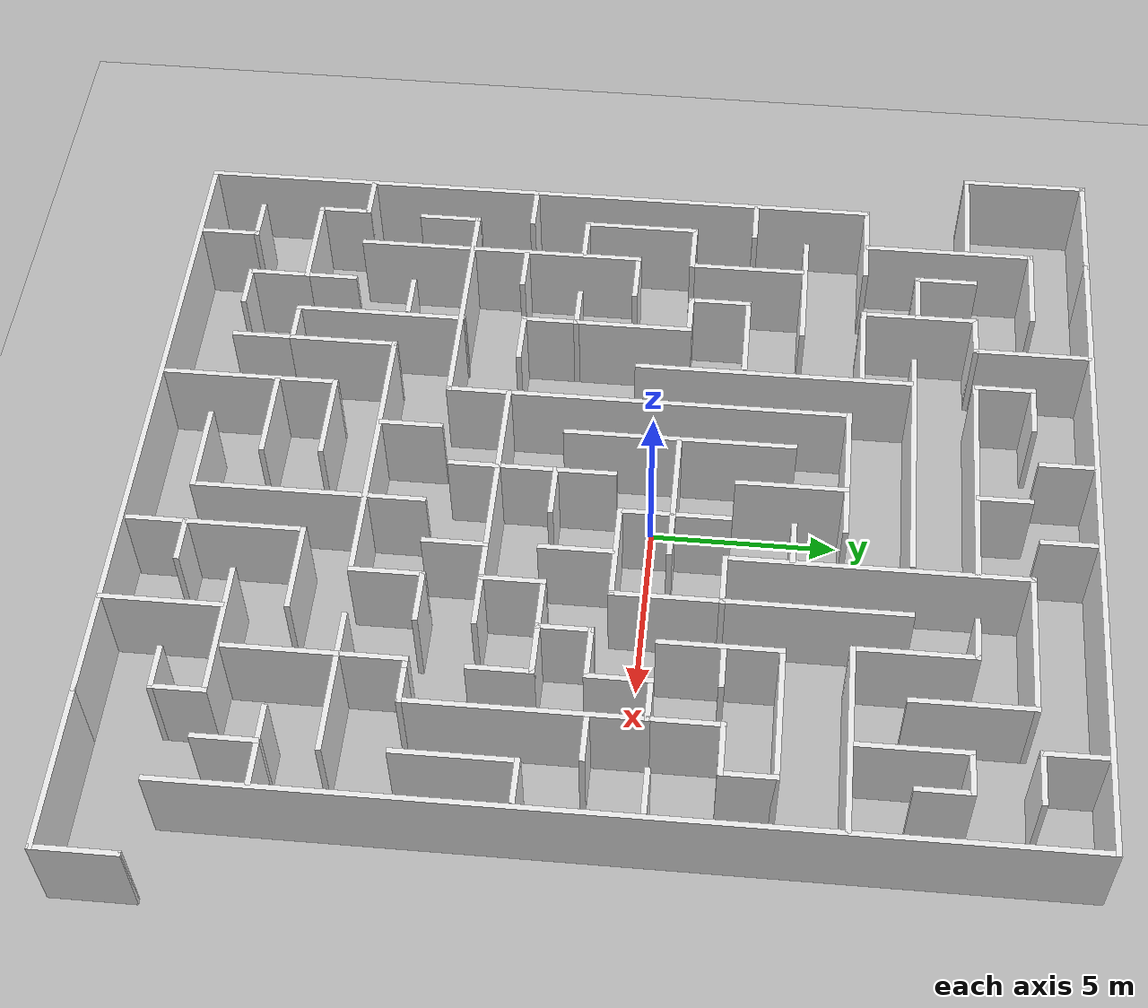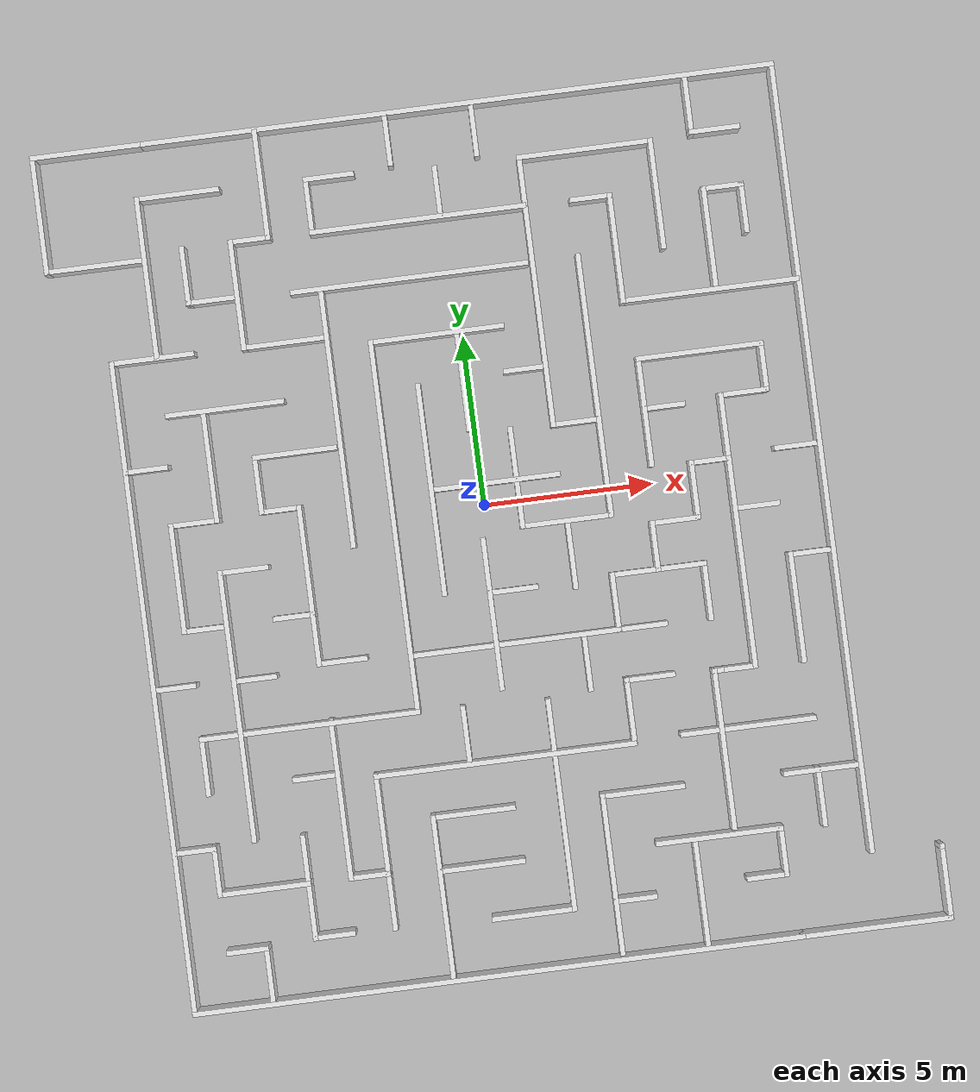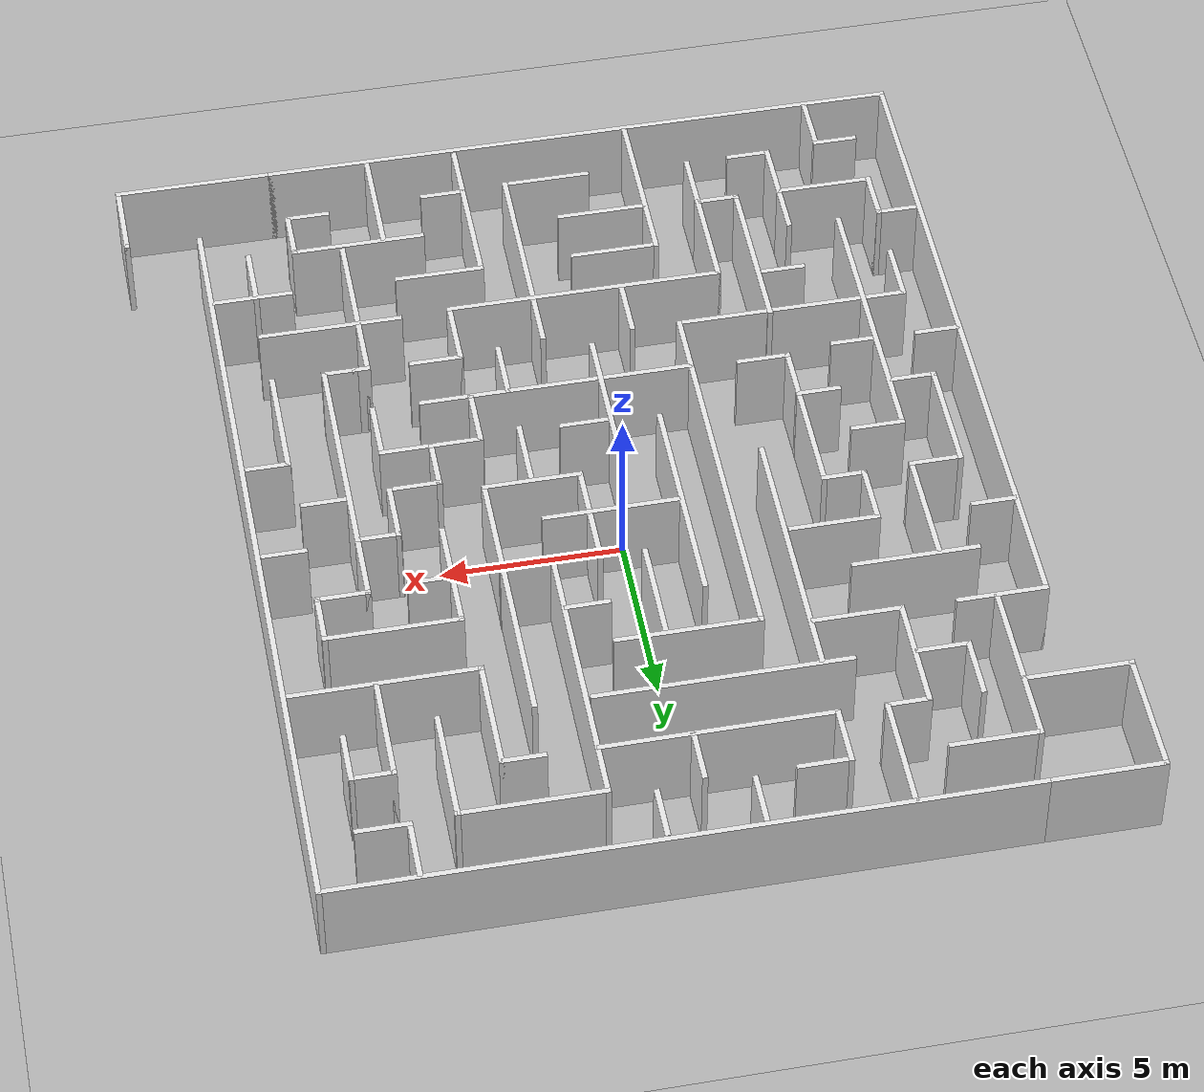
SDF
<sdf version='1.9'>
  <world name='default'>
    <light name='sun' type='directional'>
      <cast_shadows>1</cast_shadows>
      <pose>0 0 10 0 -0 0</pose>
      <diffuse>0.8 0.8 0.8 1</diffuse>
      <specular>0.2 0.2 0.2 1</specular>
      <attenuation>
        <range>1000</range>
        <constant>0.9</constant>
        <linear>0.01</linear>
        <quadratic>0.001</quadratic>
      </attenuation>
      <direction>-0.5 0.1 -0.9</direction>
    </light>
    <model name='ground_plane'>
      <static>1</static>
      <link name='link'>
        <collision name='collision'>
          <geometry>
            <plane>
              <normal>0 0 1</normal>
              <size>100 100</size>
            </plane>
          </geometry>
          <surface>
            <friction>
              <ode>
                <mu>100</mu>
                <mu2>50</mu2>
              </ode>
              <torsional>
                <ode/>
              </torsional>
            </friction>
            <contact>
              <ode/>
            </contact>
            <bounce/>
          </surface>
        </collision>
        <visual name='visual'>
          <cast_shadows>0</cast_shadows>
          <geometry>
            <plane>
              <normal>0 0 1</normal>
              <size>100 100</size>
            </plane>
          </geometry>
          <material>
            <ambient>0.6 0.6 0.6 1</ambient>
            <diffuse>0.7 0.7 0.7 1</diffuse>
            <specular>0.1 0.1 0.1 1</specular>
          </material>
        </visual>
        <self_collide>0</self_collide>
        <enable_wind>0</enable_wind>
        <kinematic>0</kinematic>
      </link>
    </model>
    <gravity>0 0 -9.8</gravity>
    <magnetic_field>6e-06 2.3e-05 -4.2e-05</magnetic_field>
    <atmosphere type='adiabatic'/>
    <physics name='default_physics' default='0' type='ode'>
      <max_step_size>0.001</max_step_size>
      <real_time_factor>1</real_time_factor>
      <real_time_update_rate>1000</real_time_update_rate>
    </physics>

    <scene>
      <ambient>0.4 0.4 0.4 1</ambient>
      <background>0.7 0.7 0.7 1</background>
      <shadows>1</shadows>
    </scene>
    <wind/>
    <spherical_coordinates>
      <surface_model>EARTH_WGS84</surface_model>
      <latitude_deg>0</latitude_deg>
      <longitude_deg>0</longitude_deg>
      <elevation>0</elevation>
      <heading_deg>0</heading_deg>
    </spherical_coordinates>
    <model name='maze'>
      <pose>0.076161 -0.985073 0 0 -0 0</pose>
      <link name='Wall_10'>
        <collision name='Wall_10_Collision'>
          <geometry>
            <box>
              <size>18 0.15 2.5</size>
            </box>
          </geometry>
          <pose>0 0 1.25 0 -0 0</pose>
          <surface>
            <contact>
              <ode/>
            </contact>
            <bounce/>
            <friction>
              <torsional>
                <ode/>
              </torsional>
              <ode/>
            </friction>
          </surface>
        </collision>
        <visual name='Wall_10_Visual'>
          <pose>0 0 1.25 0 -0 0</pose>
          <geometry>
            <box>
              <size>18 0.15 2.5</size>
            </box>
          </geometry>
          <material>
              <ambient>1 1 1 1</ambient>
              <diffuse>0.9 0.9 0.9 1</diffuse>
              <specular>0.1 0.1 0.1 1</specular>
            </material>
        </visual>
        <pose>-1.40681 -12.6653 0 0 -0 0</pose>
        <self_collide>0</self_collide>
        <enable_wind>0</enable_wind>
        <kinematic>0</kinematic>
      </link>
      <link name='Wall_100'>
        <collision name='Wall_100_Collision'>
          <geometry>
            <box>
              <size>1.5 0.15 2.5</size>
            </box>
          </geometry>
          <pose>0 0 1.25 0 -0 0</pose>
          <surface>
            <contact>
              <ode/>
            </contact>
            <bounce/>
            <friction>
              <torsional>
                <ode/>
              </torsional>
              <ode/>
            </friction>
          </surface>
        </collision>
        <visual name='Wall_100_Visual'>
          <pose>0 0 1.25 0 -0 0</pose>
          <geometry>
            <box>
              <size>1.5 0.15 2.5</size>
            </box>
          </geometry>
          <material>
              <ambient>1 1 1 1</ambient>
              <diffuse>0.9 0.9 0.9 1</diffuse>
              <specular>0.1 0.1 0.1 1</specular>
            </material>
        </visual>
        <pose>4.69711 -0.840511 0 0 -0 1.5708</pose>
        <self_collide>0</self_collide>
        <enable_wind>0</enable_wind>
        <kinematic>0</kinematic>
      </link>
      <link name='Wall_101'>
        <collision name='Wall_101_Collision'>
          <geometry>
            <box>
              <size>1.5 0.15 2.5</size>
            </box>
          </geometry>
          <pose>0 0 1.25 0 -0 0</pose>
          <surface>
            <contact>
              <ode/>
            </contact>
            <bounce/>
            <friction>
              <torsional>
                <ode/>
              </torsional>
              <ode/>
            </friction>
          </surface>
        </collision>
        <visual name='Wall_101_Visual'>
          <pose>0 0 1.25 0 -0 0</pose>
          <geometry>
            <box>
              <size>1.5 0.15 2.5</size>
            </box>
          </geometry>
          <material>
              <ambient>1 1 1 1</ambient>
              <diffuse>0.9 0.9 0.9 1</diffuse>
              <specular>0.1 0.1 0.1 1</specular>
            </material>
        </visual>
        <pose>5.37211 -0.165511 0 0 -0 0</pose>
        <self_collide>0</self_collide>
        <enable_wind>0</enable_wind>
        <kinematic>0</kinematic>
      </link>
      <link name='Wall_102'>
        <collision name='Wall_102_Collision'>
          <geometry>
            <box>
              <size>1.75 0.15 2.5</size>
            </box>
          </geometry>
          <pose>0 0 1.25 0 -0 0</pose>
          <surface>
            <contact>
              <ode/>
            </contact>
            <bounce/>
            <friction>
              <torsional>
                <ode/>
              </torsional>
              <ode/>
            </friction>
          </surface>
        </collision>
        <visual name='Wall_102_Visual'>
          <pose>0 0 1.25 0 -0 0</pose>
          <geometry>
            <box>
              <size>1.75 0.15 2.5</size>
            </box>
          </geometry>
          <material>
              <ambient>1 1 1 1</ambient>
              <diffuse>0.9 0.9 0.9 1</diffuse>
              <specular>0.1 0.1 0.1 1</specular>
            </material>
        </visual>
        <pose>6.04711 0.634489 0 0 -0 1.5708</pose>
        <self_collide>0</self_collide>
        <enable_wind>0</enable_wind>
        <kinematic>0</kinematic>
      </link>
      <link name='Wall_103'>
        <collision name='Wall_103_Collision'>
          <geometry>
            <box>
              <size>1.25 0.15 2.5</size>
            </box>
          </geometry>
          <pose>0 0 1.25 0 -0 0</pose>
          <surface>
            <contact>
              <ode/>
            </contact>
            <bounce/>
            <friction>
              <torsional>
                <ode/>
              </torsional>
              <ode/>
            </friction>
          </surface>
        </collision>
        <visual name='Wall_103_Visual'>
          <pose>0 0 1.25 0 -0 0</pose>
          <geometry>
            <box>
              <size>1.25 0.15 2.5</size>
            </box>
          </geometry>
          <material>
              <ambient>1 1 1 1</ambient>
              <diffuse>0.9 0.9 0.9 1</diffuse>
              <specular>0.1 0.1 0.1 1</specular>
            </material>
        </visual>
        <pose>6.59711 1.43449 0 0 -0 0</pose>
        <self_collide>0</self_collide>
        <enable_wind>0</enable_wind>
        <kinematic>0</kinematic>
      </link>
      <link name='Wall_104'>
        <collision name='Wall_104_Collision'>
          <geometry>
            <box>
              <size>6.25 0.15 2.5</size>
            </box>
          </geometry>
          <pose>0 0 1.25 0 -0 0</pose>
          <surface>
            <contact>
              <ode/>
            </contact>
            <bounce/>
            <friction>
              <torsional>
                <ode/>
              </torsional>
              <ode/>
            </friction>
          </surface>
        </collision>
        <visual name='Wall_104_Visual'>
          <pose>0 0 1.25 0 -0 0</pose>
          <geometry>
            <box>
              <size>6.25 0.15 2.5</size>
            </box>
          </geometry>
          <material>
              <ambient>1 1 1 1</ambient>
              <diffuse>0.9 0.9 0.9 1</diffuse>
              <specular>0.1 0.1 0.1 1</specular>
            </material>
        </visual>
        <pose>7.14711 -1.61551 0 0 -0 -1.5708</pose>
        <self_collide>0</self_collide>
        <enable_wind>0</enable_wind>
        <kinematic>0</kinematic>
      </link>
      <link name='Wall_105'>
        <collision name='Wall_105_Collision'>
          <geometry>
            <box>
              <size>1 0.15 2.5</size>
            </box>
          </geometry>
          <pose>0 0 1.25 0 -0 0</pose>
          <surface>
            <contact>
              <ode/>
            </contact>
            <bounce/>
            <friction>
              <torsional>
                <ode/>
              </torsional>
              <ode/>
            </friction>
          </surface>
        </collision>
        <visual name='Wall_105_Visual'>
          <pose>0 0 1.25 0 -0 0</pose>
          <geometry>
            <box>
              <size>1 0.15 2.5</size>
            </box>
          </geometry>
          <material>
              <ambient>1 1 1 1</ambient>
              <diffuse>0.9 0.9 0.9 1</diffuse>
              <specular>0.1 0.1 0.1 1</specular>
            </material>
        </visual>
        <pose>6.72211 -4.66551 0 0 -0 3.14159</pose>
        <self_collide>0</self_collide>
        <enable_wind>0</enable_wind>
        <kinematic>0</kinematic>
      </link>
      <link name='Wall_106'>
        <collision name='Wall_106_Collision'>
          <geometry>
            <box>
              <size>0.5 0.15 2.5</size>
            </box>
          </geometry>
          <pose>0 0 1.25 0 -0 0</pose>
          <surface>
            <contact>
              <ode/>
            </contact>
            <bounce/>
            <friction>
              <torsional>
                <ode/>
              </torsional>
              <ode/>
            </friction>
          </surface>
        </collision>
        <visual name='Wall_106_Visual'>
          <pose>0 0 1.25 0 -0 0</pose>
          <geometry>
            <box>
              <size>0.5 0.15 2.5</size>
            </box>
          </geometry>
          <material>
              <ambient>1 1 1 1</ambient>
              <diffuse>0.9 0.9 0.9 1</diffuse>
              <specular>0.1 0.1 0.1 1</specular>
            </material>
        </visual>
        <pose>6.12211 -4.66551 0 0 -0 3.14159</pose>
        <self_collide>0</self_collide>
        <enable_wind>0</enable_wind>
        <kinematic>0</kinematic>
      </link>
      <link name='Wall_107'>
        <collision name='Wall_107_Collision'>
          <geometry>
            <box>
              <size>4.75 0.15 2.5</size>
            </box>
          </geometry>
          <pose>0 0 1.25 0 -0 0</pose>
          <surface>
            <contact>
              <ode/>
            </contact>
            <bounce/>
            <friction>
              <torsional>
                <ode/>
              </torsional>
              <ode/>
            </friction>
          </surface>
        </collision>
        <visual name='Wall_107_Visual'>
          <pose>0 0 1.25 0 -0 0</pose>
          <geometry>
            <box>
              <size>4.75 0.15 2.5</size>
            </box>
          </geometry>
          <material>
              <ambient>1 1 1 1</ambient>
              <diffuse>0.9 0.9 0.9 1</diffuse>
              <specular>0.1 0.1 0.1 1</specular>
            </material>
        </visual>
        <pose>5.94711 -6.96551 0 0 -0 -1.5708</pose>
        <self_collide>0</self_collide>
        <enable_wind>0</enable_wind>
        <kinematic>0</kinematic>
      </link>
      <link name='Wall_109'>
        <collision name='Wall_109_Collision'>
          <geometry>
            <box>
              <size>4.5 0.15 2.5</size>
            </box>
          </geometry>
          <pose>0 0 1.25 0 -0 0</pose>
          <surface>
            <contact>
              <ode/>
            </contact>
            <bounce/>
            <friction>
              <torsional>
                <ode/>
              </torsional>
              <ode/>
            </friction>
          </surface>
        </collision>
        <visual name='Wall_109_Visual'>
          <pose>0 0 1.25 0 -0 0</pose>
          <geometry>
            <box>
              <size>4.5 0.15 2.5</size>
            </box>
          </geometry>
          <material>
              <ambient>1 1 1 1</ambient>
              <diffuse>0.9 0.9 0.9 1</diffuse>
              <specular>0.1 0.1 0.1 1</specular>
            </material>
        </visual>
        <pose>-0.252522 -2.20089 0 0 -0 -1.5708</pose>
        <self_collide>0</self_collide>
        <enable_wind>0</enable_wind>
        <kinematic>0</kinematic>
      </link>
      <link name='Wall_111'>
        <collision name='Wall_111_Collision'>
          <geometry>
            <box>
              <size>1.5 0.15 2.5</size>
            </box>
          </geometry>
          <pose>0 0 1.25 0 -0 0</pose>
          <surface>
            <contact>
              <ode/>
            </contact>
            <bounce/>
            <friction>
              <torsional>
                <ode/>
              </torsional>
              <ode/>
            </friction>
          </surface>
        </collision>
        <visual name='Wall_111_Visual'>
          <pose>0 0 1.25 0 -0 0</pose>
          <geometry>
            <box>
              <size>1.5 0.15 2.5</size>
            </box>
          </geometry>
          <material>
              <ambient>1 1 1 1</ambient>
              <diffuse>0.9 0.9 0.9 1</diffuse>
              <specular>0.1 0.1 0.1 1</specular>
            </material>
        </visual>
        <pose>0.422478 -1.57708 0 0 -0 0</pose>
        <self_collide>0</self_collide>
        <enable_wind>0</enable_wind>
        <kinematic>0</kinematic>
      </link>
      <link name='Wall_113'>
        <collision name='Wall_113_Collision'>
          <geometry>
            <box>
              <size>3 0.15 2.5</size>
            </box>
          </geometry>
          <pose>0 0 1.25 0 -0 0</pose>
          <surface>
            <contact>
              <ode/>
            </contact>
            <bounce/>
            <friction>
              <torsional>
                <ode/>
              </torsional>
              <ode/>
            </friction>
          </surface>
        </collision>
        <visual name='Wall_113_Visual'>
          <pose>0 0 1.25 0 -0 0</pose>
          <geometry>
            <box>
              <size>3 0.15 2.5</size>
            </box>
          </geometry>
          <material>
              <ambient>1 1 1 1</ambient>
              <diffuse>0.9 0.9 0.9 1</diffuse>
              <specular>0.1 0.1 0.1 1</specular>
            </material>
        </visual>
        <pose>-0.252522 4.66298 0 0 -0 -1.5708</pose>
        <self_collide>0</self_collide>
        <enable_wind>0</enable_wind>
        <kinematic>0</kinematic>
      </link>
      <link name='Wall_115'>
        <collision name='Wall_115_Collision'>
          <geometry>
            <box>
              <size>6.25 0.15 2.5</size>
            </box>
          </geometry>
          <pose>0 0 1.25 0 -0 0</pose>
          <surface>
            <contact>
              <ode/>
            </contact>
            <bounce/>
            <friction>
              <torsional>
                <ode/>
              </torsional>
              <ode/>
            </friction>
          </surface>
        </collision>
        <visual name='Wall_115_Visual'>
          <pose>0 0 1.25 0 -0 0</pose>
          <geometry>
            <box>
              <size>6.25 0.15 2.5</size>
            </box>
          </geometry>
          <material>
              <ambient>1 1 1 1</ambient>
              <diffuse>0.9 0.9 0.9 1</diffuse>
              <specular>0.1 0.1 0.1 1</specular>
            </material>
        </visual>
        <pose>-1.56507 1.61746 0 0 -0 -1.5708</pose>
        <self_collide>0</self_collide>
        <enable_wind>0</enable_wind>
        <kinematic>0</kinematic>
      </link>
      <link name='Wall_117'>
        <collision name='Wall_117_Collision'>
          <geometry>
            <box>
              <size>3.75 0.15 2.5</size>
            </box>
          </geometry>
          <pose>0 0 1.25 0 -0 0</pose>
          <surface>
            <contact>
              <ode/>
            </contact>
            <bounce/>
            <friction>
              <torsional>
                <ode/>
              </torsional>
              <ode/>
            </friction>
          </surface>
        </collision>
        <visual name='Wall_117_Visual'>
          <pose>0 0 1.25 0 -0 0</pose>
          <geometry>
            <box>
              <size>3.75 0.15 2.5</size>
            </box>
          </geometry>
          <material>
              <ambient>1 1 1 1</ambient>
              <diffuse>0.9 0.9 0.9 1</diffuse>
              <specular>0.1 0.1 0.1 1</specular>
            </material>
        </visual>
        <pose>0.354254 1.60485 0 0 -0 0</pose>
        <self_collide>0</self_collide>
        <enable_wind>0</enable_wind>
        <kinematic>0</kinematic>
      </link>
      <link name='Wall_119'>
        <collision name='Wall_119_Collision'>
          <geometry>
            <box>
              <size>3 0.15 2.5</size>
            </box>
          </geometry>
          <pose>0 0 1.25 0 -0 0</pose>
          <surface>
            <contact>
              <ode/>
            </contact>
            <bounce/>
            <friction>
              <torsional>
                <ode/>
              </torsional>
              <ode/>
            </friction>
          </surface>
        </collision>
        <visual name='Wall_119_Visual'>
          <pose>0 0 1.25 0 -0 0</pose>
          <geometry>
            <box>
              <size>3 0.15 2.5</size>
            </box>
          </geometry>
          <material>
              <ambient>1 1 1 1</ambient>
              <diffuse>0.9 0.9 0.9 1</diffuse>
              <specular>0.1 0.1 0.1 1</specular>
            </material>
        </visual>
        <pose>0.940702 1.6515 0 0 -0 -1.5708</pose>
        <self_collide>0</self_collide>
        <enable_wind>0</enable_wind>
        <kinematic>0</kinematic>
      </link>
      <link name='Wall_120'>
        <collision name='Wall_120_Collision'>
          <geometry>
            <box>
              <size>2.75 0.15 2.5</size>
            </box>
          </geometry>
          <pose>0 0 1.25 0 -0 0</pose>
          <surface>
            <contact>
              <ode/>
            </contact>
            <bounce/>
            <friction>
              <torsional>
                <ode/>
              </torsional>
              <ode/>
            </friction>
          </surface>
        </collision>
        <visual name='Wall_120_Visual'>
          <pose>0 0 1.25 0 -0 0</pose>
          <geometry>
            <box>
              <size>2.75 0.15 2.5</size>
            </box>
          </geometry>
          <material>
              <ambient>1 1 1 1</ambient>
              <diffuse>0.9 0.9 0.9 1</diffuse>
              <specular>0.1 0.1 0.1 1</specular>
            </material>
        </visual>
        <pose>2.2407 0.226497 0 0 -0 0</pose>
        <self_collide>0</self_collide>
        <enable_wind>0</enable_wind>
        <kinematic>0</kinematic>
      </link>
      <link name='Wall_122'>
        <collision name='Wall_122_Collision'>
          <geometry>
            <box>
              <size>7.75 0.15 2.5</size>
            </box>
          </geometry>
          <pose>0 0 1.25 0 -0 0</pose>
          <surface>
            <contact>
              <ode/>
            </contact>
            <bounce/>
            <friction>
              <torsional>
                <ode/>
              </torsional>
              <ode/>
            </friction>
          </surface>
        </collision>
        <visual name='Wall_122_Visual'>
          <pose>0 0 1.25 0 -0 0</pose>
          <geometry>
            <box>
              <size>7.75 0.15 2.5</size>
            </box>
          </geometry>
          <material>
              <ambient>1 1 1 1</ambient>
              <diffuse>0.9 0.9 0.9 1</diffuse>
              <specular>0.1 0.1 0.1 1</specular>
            </material>
        </visual>
        <pose>3.5407 4.0265 0 0 -0 1.5708</pose>
        <self_collide>0</self_collide>
        <enable_wind>0</enable_wind>
        <kinematic>0</kinematic>
      </link>
      <link name='Wall_124'>
        <collision name='Wall_124_Collision'>
          <geometry>
            <box>
              <size>2 0.15 2.5</size>
            </box>
          </geometry>
          <pose>0 0 1.25 0 -0 0</pose>
          <surface>
            <contact>
              <ode/>
            </contact>
            <bounce/>
            <friction>
              <torsional>
                <ode/>
              </torsional>
              <ode/>
            </friction>
          </surface>
        </collision>
        <visual name='Wall_124_Visual'>
          <pose>0 0 1.25 0 -0 0</pose>
          <geometry>
            <box>
              <size>2 0.15 2.5</size>
            </box>
          </geometry>
          <material>
              <ambient>1 1 1 1</ambient>
              <diffuse>0.9 0.9 0.9 1</diffuse>
              <specular>0.1 0.1 0.1 1</specular>
            </material>
        </visual>
        <pose>2.25325 -0.791789 0 0 -0 -1.5708</pose>
        <self_collide>0</self_collide>
        <enable_wind>0</enable_wind>
        <kinematic>0</kinematic>
      </link>
      <link name='Wall_129'>
        <collision name='Wall_129_Collision'>
          <geometry>
            <box>
              <size>4.75 0.15 2.5</size>
            </box>
          </geometry>
          <pose>0 0 1.25 0 -0 0</pose>
          <surface>
            <contact>
              <ode/>
            </contact>
            <bounce/>
            <friction>
              <torsional>
                <ode/>
              </torsional>
              <ode/>
            </friction>
          </surface>
        </collision>
        <visual name='Wall_129_Visual'>
          <pose>0 0 1.25 0 -0 0</pose>
          <geometry>
            <box>
              <size>4.75 0.15 2.5</size>
            </box>
          </geometry>
          <material>
              <ambient>1 1 1 1</ambient>
              <diffuse>0.9 0.9 0.9 1</diffuse>
              <specular>0.1 0.1 0.1 1</specular>
            </material>
        </visual>
        <pose>2.25325 -10.1752 0 0 -0 1.5708</pose>
        <self_collide>0</self_collide>
        <enable_wind>0</enable_wind>
        <kinematic>0</kinematic>
      </link>
      <link name='Wall_13'>
        <collision name='Wall_13_Collision'>
          <geometry>
            <box>
              <size>3.25 0.15 2.5</size>
            </box>
          </geometry>
          <pose>0 0 1.25 0 -0 0</pose>
          <surface>
            <contact>
              <ode/>
            </contact>
            <bounce/>
            <friction>
              <torsional>
                <ode/>
              </torsional>
              <ode/>
            </friction>
          </surface>
        </collision>
        <visual name='Wall_13_Visual'>
          <pose>0 0 1.25 0 -0 0</pose>
          <geometry>
            <box>
              <size>3.25 0.15 2.5</size>
            </box>
          </geometry>
          <material>
              <ambient>1 1 1 1</ambient>
              <diffuse>0.9 0.9 0.9 1</diffuse>
              <specular>0.1 0.1 0.1 1</specular>
            </material>
        </visual>
        <pose>-5.35339 11.0598 0 0 -0 -1.5708</pose>
        <self_collide>0</self_collide>
        <enable_wind>0</enable_wind>
        <kinematic>0</kinematic>
      </link>
      <link name='Wall_130'>
        <collision name='Wall_130_Collision'>
          <geometry>
            <box>
              <size>2.5 0.15 2.5</size>
            </box>
          </geometry>
          <pose>0 0 1.25 0 -0 0</pose>
          <surface>
            <contact>
              <ode/>
            </contact>
            <bounce/>
            <friction>
              <torsional>
                <ode/>
              </torsional>
              <ode/>
            </friction>
          </surface>
        </collision>
        <visual name='Wall_130_Visual'>
          <pose>0 0 1.25 0 -0 0</pose>
          <geometry>
            <box>
              <size>2.5 0.15 2.5</size>
            </box>
          </geometry>
          <material>
              <ambient>1 1 1 1</ambient>
              <diffuse>0.9 0.9 0.9 1</diffuse>
              <specular>0.1 0.1 0.1 1</specular>
            </material>
        </visual>
        <pose>3.42825 -7.87519 0 0 -0 0</pose>
        <self_collide>0</self_collide>
        <enable_wind>0</enable_wind>
        <kinematic>0</kinematic>
      </link>
      <link name='Wall_132'>
        <collision name='Wall_132_Collision'>
          <geometry>
            <box>
              <size>1.25 0.15 2.5</size>
            </box>
          </geometry>
          <pose>0 0 1.25 0 -0 0</pose>
          <surface>
            <contact>
              <ode/>
            </contact>
            <bounce/>
            <friction>
              <torsional>
                <ode/>
              </torsional>
              <ode/>
            </friction>
          </surface>
        </collision>
        <visual name='Wall_132_Visual'>
          <pose>0 0 1.25 0 -0 0</pose>
          <geometry>
            <box>
              <size>1.25 0.15 2.5</size>
            </box>
          </geometry>
          <material>
              <ambient>1 1 1 1</ambient>
              <diffuse>0.9 0.9 0.9 1</diffuse>
              <specular>0.1 0.1 0.1 1</specular>
            </material>
        </visual>
        <pose>2.84302 -10.9638 0 0 -0 0</pose>
        <self_collide>0</self_collide>
        <enable_wind>0</enable_wind>
        <kinematic>0</kinematic>
      </link>
      <link name='Wall_134'>
        <collision name='Wall_134_Collision'>
          <geometry>
            <box>
              <size>3.75 0.15 2.5</size>
            </box>
          </geometry>
          <pose>0 0 1.25 0 -0 0</pose>
          <surface>
            <contact>
              <ode/>
            </contact>
            <bounce/>
            <friction>
              <torsional>
                <ode/>
              </torsional>
              <ode/>
            </friction>
          </surface>
        </collision>
        <visual name='Wall_134_Visual'>
          <pose>0 0 1.25 0 -0 0</pose>
          <geometry>
            <box>
              <size>3.75 0.15 2.5</size>
            </box>
          </geometry>
          <material>
              <ambient>1 1 1 1</ambient>
              <diffuse>0.9 0.9 0.9 1</diffuse>
              <specular>0.1 0.1 0.1 1</specular>
            </material>
        </visual>
        <pose>5.48512 -9.45236 0 0 -0 0</pose>
        <self_collide>0</self_collide>
        <enable_wind>0</enable_wind>
        <kinematic>0</kinematic>
      </link>
      <link name='Wall_135'>
        <collision name='Wall_135_Collision'>
          <geometry>
            <box>
              <size>1.5 0.15 2.5</size>
            </box>
          </geometry>
          <pose>0 0 1.25 0 -0 0</pose>
          <surface>
            <contact>
              <ode/>
            </contact>
            <bounce/>
            <friction>
              <torsional>
                <ode/>
              </torsional>
              <ode/>
            </friction>
          </surface>
        </collision>
        <visual name='Wall_135_Visual'>
          <pose>0 0 1.25 0 -0 0</pose>
          <geometry>
            <box>
              <size>1.5 0.15 2.5</size>
            </box>
          </geometry>
          <material>
              <ambient>1 1 1 1</ambient>
              <diffuse>0.9 0.9 0.9 1</diffuse>
              <specular>0.1 0.1 0.1 1</specular>
            </material>
        </visual>
        <pose>7.28512 -10.1274 0 0 -0 -1.5708</pose>
        <self_collide>0</self_collide>
        <enable_wind>0</enable_wind>
        <kinematic>0</kinematic>
      </link>
      <link name='Wall_136'>
        <collision name='Wall_136_Collision'>
          <geometry>
            <box>
              <size>1.25 0.15 2.5</size>
            </box>
          </geometry>
          <pose>0 0 1.25 0 -0 0</pose>
          <surface>
            <contact>
              <ode/>
            </contact>
            <bounce/>
            <friction>
              <torsional>
                <ode/>
              </torsional>
              <ode/>
            </friction>
          </surface>
        </collision>
        <visual name='Wall_136_Visual'>
          <pose>0 0 1.25 0 -0 0</pose>
          <geometry>
            <box>
              <size>1.25 0.15 2.5</size>
            </box>
          </geometry>
          <material>
              <ambient>1 1 1 1</ambient>
              <diffuse>0.9 0.9 0.9 1</diffuse>
              <specular>0.1 0.1 0.1 1</specular>
            </material>
        </visual>
        <pose>6.73512 -10.8024 0 0 -0 3.14159</pose>
        <self_collide>0</self_collide>
        <enable_wind>0</enable_wind>
        <kinematic>0</kinematic>
      </link>
      <link name='Wall_138'>
        <collision name='Wall_138_Collision'>
          <geometry>
            <box>
              <size>3.25 0.15 2.5</size>
            </box>
          </geometry>
          <pose>0 0 1.25 0 -0 0</pose>
          <surface>
            <contact>
              <ode/>
            </contact>
            <bounce/>
            <friction>
              <torsional>
                <ode/>
              </torsional>
              <ode/>
            </friction>
          </surface>
        </collision>
        <visual name='Wall_138_Visual'>
          <pose>0 0 1.25 0 -0 0</pose>
          <geometry>
            <box>
              <size>3.25 0.15 2.5</size>
            </box>
          </geometry>
          <material>
              <ambient>1 1 1 1</ambient>
              <diffuse>0.9 0.9 0.9 1</diffuse>
              <specular>0.1 0.1 0.1 1</specular>
            </material>
        </visual>
        <pose>4.75902 -11.0819 0 0 -0 -1.5708</pose>
        <self_collide>0</self_collide>
        <enable_wind>0</enable_wind>
        <kinematic>0</kinematic>
      </link>
      <link name='Wall_14'>
        <collision name='Wall_14_Collision'>
          <geometry>
            <box>
              <size>1.25 0.15 2.5</size>
            </box>
          </geometry>
          <pose>0 0 1.25 0 -0 0</pose>
          <surface>
            <contact>
              <ode/>
            </contact>
            <bounce/>
            <friction>
              <torsional>
                <ode/>
              </torsional>
              <ode/>
            </friction>
          </surface>
        </collision>
        <visual name='Wall_14_Visual'>
          <pose>0 0 1.25 0 -0 0</pose>
          <geometry>
            <box>
              <size>1.25 0.15 2.5</size>
            </box>
          </geometry>
          <material>
              <ambient>1 1 1 1</ambient>
              <diffuse>0.9 0.9 0.9 1</diffuse>
              <specular>0.1 0.1 0.1 1</specular>
            </material>
        </visual>
        <pose>-5.90339 9.5098 0 0 -0 3.14159</pose>
        <self_collide>0</self_collide>
        <enable_wind>0</enable_wind>
        <kinematic>0</kinematic>
      </link>
      <link name='Wall_140'>
        <collision name='Wall_140_Collision'>
          <geometry>
            <box>
              <size>2.25 0.15 2.5</size>
            </box>
          </geometry>
          <pose>0 0 1.25 0 -0 0</pose>
          <surface>
            <contact>
              <ode/>
            </contact>
            <bounce/>
            <friction>
              <torsional>
                <ode/>
              </torsional>
              <ode/>
            </friction>
          </surface>
        </collision>
        <visual name='Wall_140_Visual'>
          <pose>0 0 1.25 0 -0 0</pose>
          <geometry>
            <box>
              <size>2.25 0.15 2.5</size>
            </box>
          </geometry>
          <material>
              <ambient>1 1 1 1</ambient>
              <diffuse>0.9 0.9 0.9 1</diffuse>
              <specular>0.1 0.1 0.1 1</specular>
            </material>
        </visual>
        <pose>8.68079 -7.90117 0 0 -0 3.14159</pose>
        <self_collide>0</self_collide>
        <enable_wind>0</enable_wind>
        <kinematic>0</kinematic>
      </link>
      <link name='Wall_142'>
        <collision name='Wall_142_Collision'>
          <geometry>
            <box>
              <size>1.75 0.15 2.5</size>
            </box>
          </geometry>
          <pose>0 0 1.25 0 -0 0</pose>
          <surface>
            <contact>
              <ode/>
            </contact>
            <bounce/>
            <friction>
              <torsional>
                <ode/>
              </torsional>
              <ode/>
            </friction>
          </surface>
        </collision>
        <visual name='Wall_142_Visual'>
          <pose>0 0 1.25 0 -0 0</pose>
          <geometry>
            <box>
              <size>1.75 0.15 2.5</size>
            </box>
          </geometry>
          <material>
              <ambient>1 1 1 1</ambient>
              <diffuse>0.9 0.9 0.9 1</diffuse>
              <specular>0.1 0.1 0.1 1</specular>
            </material>
        </visual>
        <pose>8.57734 -8.70116 0 0 -0 -1.5708</pose>
        <self_collide>0</self_collide>
        <enable_wind>0</enable_wind>
        <kinematic>0</kinematic>
      </link>
      <link name='Wall_144'>
        <collision name='Wall_144_Collision'>
          <geometry>
            <box>
              <size>4 0.15 2.5</size>
            </box>
          </geometry>
          <pose>0 0 1.25 0 -0 0</pose>
          <surface>
            <contact>
              <ode/>
            </contact>
            <bounce/>
            <friction>
              <torsional>
                <ode/>
              </torsional>
              <ode/>
            </friction>
          </surface>
        </collision>
        <visual name='Wall_144_Visual'>
          <pose>0 0 1.25 0 -0 0</pose>
          <geometry>
            <box>
              <size>4 0.15 2.5</size>
            </box>
          </geometry>
          <material>
              <ambient>1 1 1 1</ambient>
              <diffuse>0.9 0.9 0.9 1</diffuse>
              <specular>0.1 0.1 0.1 1</specular>
            </material>
        </visual>
        <pose>6.72379 -6.38975 0 0 -0 0</pose>
        <self_collide>0</self_collide>
        <enable_wind>0</enable_wind>
        <kinematic>0</kinematic>
      </link>
      <link name='Wall_146'>
        <collision name='Wall_146_Collision'>
          <geometry>
            <box>
              <size>3.25 0.15 2.5</size>
            </box>
          </geometry>
          <pose>0 0 1.25 0 -0 0</pose>
          <surface>
            <contact>
              <ode/>
            </contact>
            <bounce/>
            <friction>
              <torsional>
                <ode/>
              </torsional>
              <ode/>
            </friction>
          </surface>
        </collision>
        <visual name='Wall_146_Visual'>
          <pose>0 0 1.25 0 -0 0</pose>
          <geometry>
            <box>
              <size>3.25 0.15 2.5</size>
            </box>
          </geometry>
          <material>
              <ambient>1 1 1 1</ambient>
              <diffuse>0.9 0.9 0.9 1</diffuse>
              <specular>0.1 0.1 0.1 1</specular>
            </material>
        </visual>
        <pose>8.57734 -3.12946 0 0 -0 1.5708</pose>
        <self_collide>0</self_collide>
        <enable_wind>0</enable_wind>
        <kinematic>0</kinematic>
      </link>
      <link name='Wall_147'>
        <collision name='Wall_147_Collision'>
          <geometry>
            <box>
              <size>1.25 0.15 2.5</size>
            </box>
          </geometry>
          <pose>0 0 1.25 0 -0 0</pose>
          <surface>
            <contact>
              <ode/>
            </contact>
            <bounce/>
            <friction>
              <torsional>
                <ode/>
              </torsional>
              <ode/>
            </friction>
          </surface>
        </collision>
        <visual name='Wall_147_Visual'>
          <pose>0 0 1.25 0 -0 0</pose>
          <geometry>
            <box>
              <size>1.25 0.15 2.5</size>
            </box>
          </geometry>
          <material>
              <ambient>1 1 1 1</ambient>
              <diffuse>0.9 0.9 0.9 1</diffuse>
              <specular>0.1 0.1 0.1 1</specular>
            </material>
        </visual>
        <pose>9.12734 -1.57946 0 0 -0 0</pose>
        <self_collide>0</self_collide>
        <enable_wind>0</enable_wind>
        <kinematic>0</kinematic>
      </link>
      <link name='Wall_149'>
        <collision name='Wall_149_Collision'>
          <geometry>
            <box>
              <size>2 0.15 2.5</size>
            </box>
          </geometry>
          <pose>0 0 1.25 0 -0 0</pose>
          <surface>
            <contact>
              <ode/>
            </contact>
            <bounce/>
            <friction>
              <torsional>
                <ode/>
              </torsional>
              <ode/>
            </friction>
          </surface>
        </collision>
        <visual name='Wall_149_Visual'>
          <pose>0 0 1.25 0 -0 0</pose>
          <geometry>
            <box>
              <size>2 0.15 2.5</size>
            </box>
          </geometry>
          <material>
              <ambient>1 1 1 1</ambient>
              <diffuse>0.9 0.9 0.9 1</diffuse>
              <specular>0.1 0.1 0.1 1</specular>
            </material>
        </visual>
        <pose>7.14711 2.35949 0 0 -0 1.5708</pose>
        <self_collide>0</self_collide>
        <enable_wind>0</enable_wind>
        <kinematic>0</kinematic>
      </link>
      <link name='Wall_15'>
        <collision name='Wall_15_Collision'>
          <geometry>
            <box>
              <size>3.25 0.15 2.5</size>
            </box>
          </geometry>
          <pose>0 0 1.25 0 -0 0</pose>
          <surface>
            <contact>
              <ode/>
            </contact>
            <bounce/>
            <friction>
              <torsional>
                <ode/>
              </torsional>
              <ode/>
            </friction>
          </surface>
        </collision>
        <visual name='Wall_15_Visual'>
          <pose>0 0 1.25 0 -0 0</pose>
          <geometry>
            <box>
              <size>3.25 0.15 2.5</size>
            </box>
          </geometry>
          <material>
              <ambient>1 1 1 1</ambient>
              <diffuse>0.9 0.9 0.9 1</diffuse>
              <specular>0.1 0.1 0.1 1</specular>
            </material>
        </visual>
        <pose>-6.45339 7.9598 0 0 -0 -1.5708</pose>
        <self_collide>0</self_collide>
        <enable_wind>0</enable_wind>
        <kinematic>0</kinematic>
      </link>
      <link name='Wall_150'>
        <collision name='Wall_150_Collision'>
          <geometry>
            <box>
              <size>1.5 0.15 2.5</size>
            </box>
          </geometry>
          <pose>0 0 1.25 0 -0 0</pose>
          <surface>
            <contact>
              <ode/>
            </contact>
            <bounce/>
            <friction>
              <torsional>
                <ode/>
              </torsional>
              <ode/>
            </friction>
          </surface>
        </collision>
        <visual name='Wall_150_Visual'>
          <pose>0 0 1.25 0 -0 0</pose>
          <geometry>
            <box>
              <size>1.5 0.15 2.5</size>
            </box>
          </geometry>
          <material>
              <ambient>1 1 1 1</ambient>
              <diffuse>0.9 0.9 0.9 1</diffuse>
              <specular>0.1 0.1 0.1 1</specular>
            </material>
        </visual>
        <pose>7.82211 3.28449 0 0 -0 0</pose>
        <self_collide>0</self_collide>
        <enable_wind>0</enable_wind>
        <kinematic>0</kinematic>
      </link>
      <link name='Wall_151'>
        <collision name='Wall_151_Collision'>
          <geometry>
            <box>
              <size>1.5 0.15 2.5</size>
            </box>
          </geometry>
          <pose>0 0 1.25 0 -0 0</pose>
          <surface>
            <contact>
              <ode/>
            </contact>
            <bounce/>
            <friction>
              <torsional>
                <ode/>
              </torsional>
              <ode/>
            </friction>
          </surface>
        </collision>
        <visual name='Wall_151_Visual'>
          <pose>0 0 1.25 0 -0 0</pose>
          <geometry>
            <box>
              <size>1.5 0.15 2.5</size>
            </box>
          </geometry>
          <material>
              <ambient>1 1 1 1</ambient>
              <diffuse>0.9 0.9 0.9 1</diffuse>
              <specular>0.1 0.1 0.1 1</specular>
            </material>
        </visual>
        <pose>8.49711 3.95949 0 0 -0 1.5708</pose>
        <self_collide>0</self_collide>
        <enable_wind>0</enable_wind>
        <kinematic>0</kinematic>
      </link>
      <link name='Wall_152'>
        <collision name='Wall_152_Collision'>
          <geometry>
            <box>
              <size>3.75 0.15 2.5</size>
            </box>
          </geometry>
          <pose>0 0 1.25 0 -0 0</pose>
          <surface>
            <contact>
              <ode/>
            </contact>
            <bounce/>
            <friction>
              <torsional>
                <ode/>
              </torsional>
              <ode/>
            </friction>
          </surface>
        </collision>
        <visual name='Wall_152_Visual'>
          <pose>0 0 1.25 0 -0 0</pose>
          <geometry>
            <box>
              <size>3.75 0.15 2.5</size>
            </box>
          </geometry>
          <material>
              <ambient>1 1 1 1</ambient>
              <diffuse>0.9 0.9 0.9 1</diffuse>
              <specular>0.1 0.1 0.1 1</specular>
            </material>
        </visual>
        <pose>6.69711 4.63449 0 0 -0 3.14159</pose>
        <self_collide>0</self_collide>
        <enable_wind>0</enable_wind>
        <kinematic>0</kinematic>
      </link>
      <link name='Wall_153'>
        <collision name='Wall_153_Collision'>
          <geometry>
            <box>
              <size>3.25 0.15 2.5</size>
            </box>
          </geometry>
          <pose>0 0 1.25 0 -0 0</pose>
          <surface>
            <contact>
              <ode/>
            </contact>
            <bounce/>
            <friction>
              <torsional>
                <ode/>
              </torsional>
              <ode/>
            </friction>
          </surface>
        </collision>
        <visual name='Wall_153_Visual'>
          <pose>0 0 1.25 0 -0 0</pose>
          <geometry>
            <box>
              <size>3.25 0.15 2.5</size>
            </box>
          </geometry>
          <material>
              <ambient>1 1 1 1</ambient>
              <diffuse>0.9 0.9 0.9 1</diffuse>
              <specular>0.1 0.1 0.1 1</specular>
            </material>
        </visual>
        <pose>4.89711 3.08449 0 0 -0 -1.5708</pose>
        <self_collide>0</self_collide>
        <enable_wind>0</enable_wind>
        <kinematic>0</kinematic>
      </link>
      <link name='Wall_155'>
        <collision name='Wall_155_Collision'>
          <geometry>
            <box>
              <size>1.25 0.15 2.5</size>
            </box>
          </geometry>
          <pose>0 0 1.25 0 -0 0</pose>
          <surface>
            <contact>
              <ode/>
            </contact>
            <bounce/>
            <friction>
              <torsional>
                <ode/>
              </torsional>
              <ode/>
            </friction>
          </surface>
        </collision>
        <visual name='Wall_155_Visual'>
          <pose>0 0 1.25 0 -0 0</pose>
          <geometry>
            <box>
              <size>1.25 0.15 2.5</size>
            </box>
          </geometry>
          <material>
              <ambient>1 1 1 1</ambient>
              <diffuse>0.9 0.9 0.9 1</diffuse>
              <specular>0.1 0.1 0.1 1</specular>
            </material>
        </visual>
        <pose>5.47255 3.17028 0 0 -0 0</pose>
        <self_collide>0</self_collide>
        <enable_wind>0</enable_wind>
        <kinematic>0</kinematic>
      </link>
      <link name='Wall_157'>
        <collision name='Wall_157_Collision'>
          <geometry>
            <box>
              <size>1.25 0.15 2.5</size>
            </box>
          </geometry>
          <pose>0 0 1.25 0 -0 0</pose>
          <surface>
            <contact>
              <ode/>
            </contact>
            <bounce/>
            <friction>
              <torsional>
                <ode/>
              </torsional>
              <ode/>
            </friction>
          </surface>
        </collision>
        <visual name='Wall_157_Visual'>
          <pose>0 0 1.25 0 -0 0</pose>
          <geometry>
            <box>
              <size>1.25 0.15 2.5</size>
            </box>
          </geometry>
          <material>
              <ambient>1 1 1 1</ambient>
              <diffuse>0.9 0.9 0.9 1</diffuse>
              <specular>0.1 0.1 0.1 1</specular>
            </material>
        </visual>
        <pose>4.12369 9.46497 0 0 -0 0</pose>
        <self_collide>0</self_collide>
        <enable_wind>0</enable_wind>
        <kinematic>0</kinematic>
      </link>
      <link name='Wall_158'>
        <collision name='Wall_158_Collision'>
          <geometry>
            <box>
              <size>3.25 0.15 2.5</size>
            </box>
          </geometry>
          <pose>0 0 1.25 0 -0 0</pose>
          <surface>
            <contact>
              <ode/>
            </contact>
            <bounce/>
            <friction>
              <torsional>
                <ode/>
              </torsional>
              <ode/>
            </friction>
          </surface>
        </collision>
        <visual name='Wall_158_Visual'>
          <pose>0 0 1.25 0 -0 0</pose>
          <geometry>
            <box>
              <size>3.25 0.15 2.5</size>
            </box>
          </geometry>
          <material>
              <ambient>1 1 1 1</ambient>
              <diffuse>0.9 0.9 0.9 1</diffuse>
              <specular>0.1 0.1 0.1 1</specular>
            </material>
        </visual>
        <pose>4.67369 7.91497 0 0 -0 -1.5708</pose>
        <self_collide>0</self_collide>
        <enable_wind>0</enable_wind>
        <kinematic>0</kinematic>
      </link>
      <link name='Wall_159'>
        <collision name='Wall_159_Collision'>
          <geometry>
            <box>
              <size>5.25 0.15 2.5</size>
            </box>
          </geometry>
          <pose>0 0 1.25 0 -0 0</pose>
          <surface>
            <contact>
              <ode/>
            </contact>
            <bounce/>
            <friction>
              <torsional>
                <ode/>
              </torsional>
              <ode/>
            </friction>
          </surface>
        </collision>
        <visual name='Wall_159_Visual'>
          <pose>0 0 1.25 0 -0 0</pose>
          <geometry>
            <box>
              <size>5.25 0.15 2.5</size>
            </box>
          </geometry>
          <material>
              <ambient>1 1 1 1</ambient>
              <diffuse>0.9 0.9 0.9 1</diffuse>
              <specular>0.1 0.1 0.1 1</specular>
            </material>
        </visual>
        <pose>7.22369 6.36497 0 0 -0 0</pose>
        <self_collide>0</self_collide>
        <enable_wind>0</enable_wind>
        <kinematic>0</kinematic>
      </link>
      <link name='Wall_16'>
        <collision name='Wall_16_Collision'>
          <geometry>
            <box>
              <size>2.5 0.15 2.5</size>
            </box>
          </geometry>
          <pose>0 0 1.25 0 -0 0</pose>
          <surface>
            <contact>
              <ode/>
            </contact>
            <bounce/>
            <friction>
              <torsional>
                <ode/>
              </torsional>
              <ode/>
            </friction>
          </surface>
        </collision>
        <visual name='Wall_16_Visual'>
          <pose>0 0 1.25 0 -0 0</pose>
          <geometry>
            <box>
              <size>2.5 0.15 2.5</size>
            </box>
          </geometry>
          <material>
              <ambient>1 1 1 1</ambient>
              <diffuse>0.9 0.9 0.9 1</diffuse>
              <specular>0.1 0.1 0.1 1</specular>
            </material>
        </visual>
        <pose>-5.27839 6.4098 0 0 -0 0</pose>
        <self_collide>0</self_collide>
        <enable_wind>0</enable_wind>
        <kinematic>0</kinematic>
      </link>
      <link name='Wall_161'>
        <collision name='Wall_161_Collision'>
          <geometry>
            <box>
              <size>3 0.15 2.5</size>
            </box>
          </geometry>
          <pose>0 0 1.25 0 -0 0</pose>
          <surface>
            <contact>
              <ode/>
            </contact>
            <bounce/>
            <friction>
              <torsional>
                <ode/>
              </torsional>
              <ode/>
            </friction>
          </surface>
        </collision>
        <visual name='Wall_161_Visual'>
          <pose>0 0 1.25 0 -0 0</pose>
          <geometry>
            <box>
              <size>3 0.15 2.5</size>
            </box>
          </geometry>
          <material>
              <ambient>1 1 1 1</ambient>
              <diffuse>0.9 0.9 0.9 1</diffuse>
              <specular>0.1 0.1 0.1 1</specular>
            </material>
        </visual>
        <pose>7.41276 7.88097 0 0 -0 1.5708</pose>
        <self_collide>0</self_collide>
        <enable_wind>0</enable_wind>
        <kinematic>0</kinematic>
      </link>
      <link name='Wall_162'>
        <collision name='Wall_162_Collision'>
          <geometry>
            <box>
              <size>1.25 0.15 2.5</size>
            </box>
          </geometry>
          <pose>0 0 1.25 0 -0 0</pose>
          <surface>
            <contact>
              <ode/>
            </contact>
            <bounce/>
            <friction>
              <torsional>
                <ode/>
              </torsional>
              <ode/>
            </friction>
          </surface>
        </collision>
        <visual name='Wall_162_Visual'>
          <pose>0 0 1.25 0 -0 0</pose>
          <geometry>
            <box>
              <size>1.25 0.15 2.5</size>
            </box>
          </geometry>
          <material>
              <ambient>1 1 1 1</ambient>
              <diffuse>0.9 0.9 0.9 1</diffuse>
              <specular>0.1 0.1 0.1 1</specular>
            </material>
        </visual>
        <pose>7.96276 9.30597 0 0 -0 0</pose>
        <self_collide>0</self_collide>
        <enable_wind>0</enable_wind>
        <kinematic>0</kinematic>
      </link>
      <link name='Wall_163'>
        <collision name='Wall_163_Collision'>
          <geometry>
            <box>
              <size>1.5 0.15 2.5</size>
            </box>
          </geometry>
          <pose>0 0 1.25 0 -0 0</pose>
          <surface>
            <contact>
              <ode/>
            </contact>
            <bounce/>
            <friction>
              <torsional>
                <ode/>
              </torsional>
              <ode/>
            </friction>
          </surface>
        </collision>
        <visual name='Wall_163_Visual'>
          <pose>0 0 1.25 0 -0 0</pose>
          <geometry>
            <box>
              <size>1.5 0.15 2.5</size>
            </box>
          </geometry>
          <material>
              <ambient>1 1 1 1</ambient>
              <diffuse>0.9 0.9 0.9 1</diffuse>
              <specular>0.1 0.1 0.1 1</specular>
            </material>
        </visual>
        <pose>8.51276 8.63097 0 0 -0 -1.5708</pose>
        <self_collide>0</self_collide>
        <enable_wind>0</enable_wind>
        <kinematic>0</kinematic>
      </link>
      <link name='Wall_167'>
        <collision name='Wall_167_Collision'>
          <geometry>
            <box>
              <size>1.5 0.15 2.5</size>
            </box>
          </geometry>
          <pose>0 0 1.25 0 -0 0</pose>
          <surface>
            <contact>
              <ode/>
            </contact>
            <bounce/>
            <friction>
              <torsional>
                <ode/>
              </torsional>
              <ode/>
            </friction>
          </surface>
        </collision>
        <visual name='Wall_167_Visual'>
          <pose>0 0 1.25 0 -0 0</pose>
          <geometry>
            <box>
              <size>1.5 0.15 2.5</size>
            </box>
          </geometry>
          <material>
              <ambient>1 1 1 1</ambient>
              <diffuse>0.9 0.9 0.9 1</diffuse>
              <specular>0.1 0.1 0.1 1</specular>
            </material>
        </visual>
        <pose>7.94942 10.9894 0 0 -0 0</pose>
        <self_collide>0</self_collide>
        <enable_wind>0</enable_wind>
        <kinematic>0</kinematic>
      </link>
      <link name='Wall_169'>
        <collision name='Wall_169_Collision'>
          <geometry>
            <box>
              <size>1.75 0.15 2.5</size>
            </box>
          </geometry>
          <pose>0 0 1.25 0 -0 0</pose>
          <surface>
            <contact>
              <ode/>
            </contact>
            <bounce/>
            <friction>
              <torsional>
                <ode/>
              </torsional>
              <ode/>
            </friction>
          </surface>
        </collision>
        <visual name='Wall_169_Visual'>
          <pose>0 0 1.25 0 -0 0</pose>
          <geometry>
            <box>
              <size>1.75 0.15 2.5</size>
            </box>
          </geometry>
          <material>
              <ambient>1 1 1 1</ambient>
              <diffuse>0.9 0.9 0.9 1</diffuse>
              <specular>0.1 0.1 0.1 1</specular>
            </material>
        </visual>
        <pose>7.27442 11.7894 0 0 -0 1.5708</pose>
        <self_collide>0</self_collide>
        <enable_wind>0</enable_wind>
        <kinematic>0</kinematic>
      </link>
      <link name='Wall_171'>
        <collision name='Wall_171_Collision'>
          <geometry>
            <box>
              <size>1.5 0.15 2.5</size>
            </box>
          </geometry>
          <pose>0 0 1.25 0 -0 0</pose>
          <surface>
            <contact>
              <ode/>
            </contact>
            <bounce/>
            <friction>
              <torsional>
                <ode/>
              </torsional>
              <ode/>
            </friction>
          </surface>
        </collision>
        <visual name='Wall_171_Visual'>
          <pose>0 0 1.25 0 -0 0</pose>
          <geometry>
            <box>
              <size>1.5 0.15 2.5</size>
            </box>
          </geometry>
          <material>
              <ambient>1 1 1 1</ambient>
              <diffuse>0.9 0.9 0.9 1</diffuse>
              <specular>0.1 0.1 0.1 1</specular>
            </material>
        </visual>
        <pose>0.993011 11.8294 0 0 -0 -1.5708</pose>
        <self_collide>0</self_collide>
        <enable_wind>0</enable_wind>
        <kinematic>0</kinematic>
      </link>
      <link name='Wall_173'>
        <collision name='Wall_173_Collision'>
          <geometry>
            <box>
              <size>1.25 0.15 2.5</size>
            </box>
          </geometry>
          <pose>0 0 1.25 0 -0 0</pose>
          <surface>
            <contact>
              <ode/>
            </contact>
            <bounce/>
            <friction>
              <torsional>
                <ode/>
              </torsional>
              <ode/>
            </friction>
          </surface>
        </collision>
        <visual name='Wall_173_Visual'>
          <pose>0 0 1.25 0 -0 0</pose>
          <geometry>
            <box>
              <size>1.25 0.15 2.5</size>
            </box>
          </geometry>
          <material>
              <ambient>1 1 1 1</ambient>
              <diffuse>0.9 0.9 0.9 1</diffuse>
              <specular>0.1 0.1 0.1 1</specular>
            </material>
        </visual>
        <pose>1.58262 4.76575 0 0 -0 0</pose>
        <self_collide>0</self_collide>
        <enable_wind>0</enable_wind>
        <kinematic>0</kinematic>
      </link>
      <link name='Wall_175'>
        <collision name='Wall_175_Collision'>
          <geometry>
            <box>
              <size>1.5 0.15 2.5</size>
            </box>
          </geometry>
          <pose>0 0 1.25 0 -0 0</pose>
          <surface>
            <contact>
              <ode/>
            </contact>
            <bounce/>
            <friction>
              <torsional>
                <ode/>
              </torsional>
              <ode/>
            </friction>
          </surface>
        </collision>
        <visual name='Wall_175_Visual'>
          <pose>0 0 1.25 0 -0 0</pose>
          <geometry>
            <box>
              <size>1.5 0.15 2.5</size>
            </box>
          </geometry>
          <material>
              <ambient>1 1 1 1</ambient>
              <diffuse>0.9 0.9 0.9 1</diffuse>
              <specular>0.1 0.1 0.1 1</specular>
            </material>
        </visual>
        <pose>5.37211 -1.51551 0 0 -0 0</pose>
        <self_collide>0</self_collide>
        <enable_wind>0</enable_wind>
        <kinematic>0</kinematic>
      </link>
      <link name='Wall_176'>
        <collision name='Wall_176_Collision'>
          <geometry>
            <box>
              <size>1.75 0.15 2.5</size>
            </box>
          </geometry>
          <pose>0 0 1.25 0 -0 0</pose>
          <surface>
            <contact>
              <ode/>
            </contact>
            <bounce/>
            <friction>
              <torsional>
                <ode/>
              </torsional>
              <ode/>
            </friction>
          </surface>
        </collision>
        <visual name='Wall_176_Visual'>
          <pose>0 0 1.25 0 -0 0</pose>
          <geometry>
            <box>
              <size>1.75 0.15 2.5</size>
            </box>
          </geometry>
          <material>
              <ambient>1 1 1 1</ambient>
              <diffuse>0.9 0.9 0.9 1</diffuse>
              <specular>0.1 0.1 0.1 1</specular>
            </material>
        </visual>
        <pose>6.04711 -2.31551 0 0 -0 -1.5708</pose>
        <self_collide>0</self_collide>
        <enable_wind>0</enable_wind>
        <kinematic>0</kinematic>
      </link>
      <link name='Wall_178'>
        <collision name='Wall_178_Collision'>
          <geometry>
            <box>
              <size>1.25 0.15 2.5</size>
            </box>
          </geometry>
          <pose>0 0 1.25 0 -0 0</pose>
          <surface>
            <contact>
              <ode/>
            </contact>
            <bounce/>
            <friction>
              <torsional>
                <ode/>
              </torsional>
              <ode/>
            </friction>
          </surface>
        </collision>
        <visual name='Wall_178_Visual'>
          <pose>0 0 1.25 0 -0 0</pose>
          <geometry>
            <box>
              <size>1.25 0.15 2.5</size>
            </box>
          </geometry>
          <material>
              <ambient>1 1 1 1</ambient>
              <diffuse>0.9 0.9 0.9 1</diffuse>
              <specular>0.1 0.1 0.1 1</specular>
            </material>
        </visual>
        <pose>9.12241 1.54923 0 0 -0 0</pose>
        <self_collide>0</self_collide>
        <enable_wind>0</enable_wind>
        <kinematic>0</kinematic>
      </link>
      <link name='Wall_18'>
        <collision name='Wall_18_Collision'>
          <geometry>
            <box>
              <size>1.75 0.15 2.5</size>
            </box>
          </geometry>
          <pose>0 0 1.25 0 -0 0</pose>
          <surface>
            <contact>
              <ode/>
            </contact>
            <bounce/>
            <friction>
              <torsional>
                <ode/>
              </torsional>
              <ode/>
            </friction>
          </surface>
        </collision>
        <visual name='Wall_18_Visual'>
          <pose>0 0 1.25 0 -0 0</pose>
          <geometry>
            <box>
              <size>1.75 0.15 2.5</size>
            </box>
          </geometry>
          <material>
              <ambient>1 1 1 1</ambient>
              <diffuse>0.9 0.9 0.9 1</diffuse>
              <specular>0.1 0.1 0.1 1</specular>
            </material>
        </visual>
        <pose>-7.88456 8.70516 0 0 -0 -1.5708</pose>
        <self_collide>0</self_collide>
        <enable_wind>0</enable_wind>
        <kinematic>0</kinematic>
      </link>
      <link name='Wall_180'>
        <collision name='Wall_180_Collision'>
          <geometry>
            <box>
              <size>1.25 0.15 2.5</size>
            </box>
          </geometry>
          <pose>0 0 1.25 0 -0 0</pose>
          <surface>
            <contact>
              <ode/>
            </contact>
            <bounce/>
            <friction>
              <torsional>
                <ode/>
              </torsional>
              <ode/>
            </friction>
          </surface>
        </collision>
        <visual name='Wall_180_Visual'>
          <pose>0 0 1.25 0 -0 0</pose>
          <geometry>
            <box>
              <size>1.25 0.15 2.5</size>
            </box>
          </geometry>
          <material>
              <ambient>1 1 1 1</ambient>
              <diffuse>0.9 0.9 0.9 1</diffuse>
              <specular>0.1 0.1 0.1 1</specular>
            </material>
        </visual>
        <pose>7.84272 -0.041733 0 0 -0 0</pose>
        <self_collide>0</self_collide>
        <enable_wind>0</enable_wind>
        <kinematic>0</kinematic>
      </link>
      <link name='Wall_182'>
        <collision name='Wall_182_Collision'>
          <geometry>
            <box>
              <size>1.5 0.15 2.5</size>
            </box>
          </geometry>
          <pose>0 0 1.25 0 -0 0</pose>
          <surface>
            <contact>
              <ode/>
            </contact>
            <bounce/>
            <friction>
              <torsional>
                <ode/>
              </torsional>
              <ode/>
            </friction>
          </surface>
        </collision>
        <visual name='Wall_182_Visual'>
          <pose>0 0 1.25 0 -0 0</pose>
          <geometry>
            <box>
              <size>1.5 0.15 2.5</size>
            </box>
          </geometry>
          <material>
              <ambient>1 1 1 1</ambient>
              <diffuse>0.9 0.9 0.9 1</diffuse>
              <specular>0.1 0.1 0.1 1</specular>
            </material>
        </visual>
        <pose>4.02211 -3.11551 0 0 -0 0</pose>
        <self_collide>0</self_collide>
        <enable_wind>0</enable_wind>
        <kinematic>0</kinematic>
      </link>
      <link name='Wall_184'>
        <collision name='Wall_184_Collision'>
          <geometry>
            <box>
              <size>1.25 0.15 2.5</size>
            </box>
          </geometry>
          <pose>0 0 1.25 0 -0 0</pose>
          <surface>
            <contact>
              <ode/>
            </contact>
            <bounce/>
            <friction>
              <torsional>
                <ode/>
              </torsional>
              <ode/>
            </friction>
          </surface>
        </collision>
        <visual name='Wall_184_Visual'>
          <pose>0 0 1.25 0 -0 0</pose>
          <geometry>
            <box>
              <size>1.25 0.15 2.5</size>
            </box>
          </geometry>
          <material>
              <ambient>1 1 1 1</ambient>
              <diffuse>0.9 0.9 0.9 1</diffuse>
              <specular>0.1 0.1 0.1 1</specular>
            </material>
        </visual>
        <pose>-6.02635 -6.26725 0 0 -0 0</pose>
        <self_collide>0</self_collide>
        <enable_wind>0</enable_wind>
        <kinematic>0</kinematic>
      </link>
      <link name='Wall_187'>
        <collision name='Wall_187_Collision'>
          <geometry>
            <box>
              <size>3.25 0.15 2.5</size>
            </box>
          </geometry>
          <pose>0 0 1.25 0 -0 0</pose>
          <surface>
            <contact>
              <ode/>
            </contact>
            <bounce/>
            <friction>
              <torsional>
                <ode/>
              </torsional>
              <ode/>
            </friction>
          </surface>
        </collision>
        <visual name='Wall_187_Visual'>
          <pose>0 0 1.25 0 -0 0</pose>
          <geometry>
            <box>
              <size>3.25 0.15 2.5</size>
            </box>
          </geometry>
          <material>
              <ambient>1 1 1 1</ambient>
              <diffuse>0.9 0.9 0.9 1</diffuse>
              <specular>0.1 0.1 0.1 1</specular>
            </material>
        </visual>
        <pose>-10.3182 12.6653 0 0 -0 3.14159</pose>
        <self_collide>0</self_collide>
        <enable_wind>0</enable_wind>
        <kinematic>0</kinematic>
      </link>
      <link name='Wall_188'>
        <collision name='Wall_188_Collision'>
          <geometry>
            <box>
              <size>3.5 0.15 2.5</size>
            </box>
          </geometry>
          <pose>0 0 1.25 0 -0 0</pose>
          <surface>
            <contact>
              <ode/>
            </contact>
            <bounce/>
            <friction>
              <torsional>
                <ode/>
              </torsional>
              <ode/>
            </friction>
          </surface>
        </collision>
        <visual name='Wall_188_Visual'>
          <pose>0 0 1.25 0 -0 0</pose>
          <geometry>
            <box>
              <size>3.5 0.15 2.5</size>
            </box>
          </geometry>
          <material>
              <ambient>1 1 1 1</ambient>
              <diffuse>0.9 0.9 0.9 1</diffuse>
              <specular>0.1 0.1 0.1 1</specular>
            </material>
        </visual>
        <pose>-11.8682 10.9903 0 0 -0 -1.5708</pose>
        <self_collide>0</self_collide>
        <enable_wind>0</enable_wind>
        <kinematic>0</kinematic>
      </link>
      <link name='Wall_189'>
        <collision name='Wall_189_Collision'>
          <geometry>
            <box>
              <size>3 0.15 2.5</size>
            </box>
          </geometry>
          <pose>0 0 1.25 0 -0 0</pose>
          <surface>
            <contact>
              <ode/>
            </contact>
            <bounce/>
            <friction>
              <torsional>
                <ode/>
              </torsional>
              <ode/>
            </friction>
          </surface>
        </collision>
        <visual name='Wall_189_Visual'>
          <pose>0 0 1.25 0 -0 0</pose>
          <geometry>
            <box>
              <size>3 0.15 2.5</size>
            </box>
          </geometry>
          <material>
              <ambient>1 1 1 1</ambient>
              <diffuse>0.9 0.9 0.9 1</diffuse>
              <specular>0.1 0.1 0.1 1</specular>
            </material>
        </visual>
        <pose>-10.4432 9.31531 0 0 -0 0</pose>
        <self_collide>0</self_collide>
        <enable_wind>0</enable_wind>
        <kinematic>0</kinematic>
      </link>
      <link name='Wall_19'>
        <collision name='Wall_19_Collision'>
          <geometry>
            <box>
              <size>1.5 0.15 2.5</size>
            </box>
          </geometry>
          <pose>0 0 1.25 0 -0 0</pose>
          <surface>
            <contact>
              <ode/>
            </contact>
            <bounce/>
            <friction>
              <torsional>
                <ode/>
              </torsional>
              <ode/>
            </friction>
          </surface>
        </collision>
        <visual name='Wall_19_Visual'>
          <pose>0 0 1.25 0 -0 0</pose>
          <geometry>
            <box>
              <size>1.5 0.15 2.5</size>
            </box>
          </geometry>
          <material>
              <ambient>1 1 1 1</ambient>
              <diffuse>0.9 0.9 0.9 1</diffuse>
              <specular>0.1 0.1 0.1 1</specular>
            </material>
        </visual>
        <pose>-7.20956 7.90516 0 0 -0 0</pose>
        <self_collide>0</self_collide>
        <enable_wind>0</enable_wind>
        <kinematic>0</kinematic>
      </link>
      <link name='Wall_192'>
        <collision name='Wall_192_Collision'>
          <geometry>
            <box>
              <size>1.75 0.15 2.5</size>
            </box>
          </geometry>
          <pose>0 0 1.25 0 -0 0</pose>
          <surface>
            <contact>
              <ode/>
            </contact>
            <bounce/>
            <friction>
              <torsional>
                <ode/>
              </torsional>
              <ode/>
            </friction>
          </surface>
        </collision>
        <visual name='Wall_192_Visual'>
          <pose>0 0 1.25 0 -0 0</pose>
          <geometry>
            <box>
              <size>1.75 0.15 2.5</size>
            </box>
          </geometry>
          <material>
              <ambient>1 1 1 1</ambient>
              <diffuse>0.9 0.9 0.9 1</diffuse>
              <specular>0.1 0.1 0.1 1</specular>
            </material>
        </visual>
        <pose>2.311 -3.92815 0 0 -0 -1.5708</pose>
        <self_collide>0</self_collide>
        <enable_wind>0</enable_wind>
        <kinematic>0</kinematic>
      </link>
      <link name='Wall_195'>
        <collision name='Wall_195_Collision'>
          <geometry>
            <box>
              <size>4.5 0.15 2.5</size>
            </box>
          </geometry>
          <pose>0 0 1.25 0 -0 0</pose>
          <surface>
            <contact>
              <ode/>
            </contact>
            <bounce/>
            <friction>
              <torsional>
                <ode/>
              </torsional>
              <ode/>
            </friction>
          </surface>
        </collision>
        <visual name='Wall_195_Visual'>
          <pose>0 0 1.25 0 -0 0</pose>
          <geometry>
            <box>
              <size>4.5 0.15 2.5</size>
            </box>
          </geometry>
          <material>
              <ambient>1 1 1 1</ambient>
              <diffuse>0.9 0.9 0.9 1</diffuse>
              <specular>0.1 0.1 0.1 1</specular>
            </material>
        </visual>
        <pose>9.69319 -12.6653 0 0 -0 0</pose>
        <self_collide>0</self_collide>
        <enable_wind>0</enable_wind>
        <kinematic>0</kinematic>
      </link>
      <link name='Wall_197'>
        <collision name='Wall_197_Collision'>
          <geometry>
            <box>
              <size>0.15 0.15 2.5</size>
            </box>
          </geometry>
          <pose>0 0 1.25 0 -0 0</pose>
          <surface>
            <contact>
              <ode/>
            </contact>
            <bounce/>
            <friction>
              <torsional>
                <ode/>
              </torsional>
              <ode/>
            </friction>
          </surface>
        </collision>
        <visual name='Wall_197_Visual'>
          <pose>0 0 1.25 0 -0 0</pose>
          <geometry>
            <box>
              <size>0.15 0.15 2.5</size>
            </box>
          </geometry>
          <material>
              <ambient>1 1 1 1</ambient>
              <diffuse>0.9 0.9 0.9 1</diffuse>
              <specular>0.1 0.1 0.1 1</specular>
            </material>
        </visual>
        <pose>11.8682 -10.5653 0 0 -0 0</pose>
        <self_collide>0</self_collide>
        <enable_wind>0</enable_wind>
        <kinematic>0</kinematic>
      </link>
      <link name='Wall_2'>
        <collision name='Wall_2_Collision'>
          <geometry>
            <box>
              <size>18.75 0.15 2.5</size>
            </box>
          </geometry>
          <pose>0 0 1.25 0 -0 0</pose>
          <surface>
            <contact>
              <ode/>
            </contact>
            <bounce/>
            <friction>
              <torsional>
                <ode/>
              </torsional>
              <ode/>
            </friction>
          </surface>
        </collision>
        <visual name='Wall_2_Visual'>
          <pose>0 0 1.25 0 -0 0</pose>
          <geometry>
            <box>
              <size>18.75 0.15 2.5</size>
            </box>
          </geometry>
          <material>
              <ambient>1 1 1 1</ambient>
              <diffuse>0.9 0.9 0.9 1</diffuse>
              <specular>0.1 0.1 0.1 1</specular>
            </material>
        </visual>
        <pose>0.531805 12.6653 0 0 -0 0</pose>
        <self_collide>0</self_collide>
        <enable_wind>0</enable_wind>
        <kinematic>0</kinematic>
      </link>
      <link name='Wall_201'>
        <collision name='Wall_201_Collision'>
          <geometry>
            <box>
              <size>2.25 0.15 2.5</size>
            </box>
          </geometry>
          <pose>0 0 1.25 0 -0 0</pose>
          <surface>
            <contact>
              <ode/>
            </contact>
            <bounce/>
            <friction>
              <torsional>
                <ode/>
              </torsional>
              <ode/>
            </friction>
          </surface>
        </collision>
        <visual name='Wall_201_Visual'>
          <pose>0 0 1.25 0 -0 0</pose>
          <geometry>
            <box>
              <size>2.25 0.15 2.5</size>
            </box>
          </geometry>
          <material>
              <ambient>1 1 1 1</ambient>
              <diffuse>0.9 0.9 0.9 1</diffuse>
              <specular>0.1 0.1 0.1 1</specular>
            </material>
        </visual>
        <pose>11.8682 -11.6153 0 0 -0 -1.5708</pose>
        <self_collide>0</self_collide>
        <enable_wind>0</enable_wind>
        <kinematic>0</kinematic>
      </link>
      <link name='Wall_21'>
        <collision name='Wall_21_Collision'>
          <geometry>
            <box>
              <size>1.5 0.15 2.5</size>
            </box>
          </geometry>
          <pose>0 0 1.25 0 -0 0</pose>
          <surface>
            <contact>
              <ode/>
            </contact>
            <bounce/>
            <friction>
              <torsional>
                <ode/>
              </torsional>
              <ode/>
            </friction>
          </surface>
        </collision>
        <visual name='Wall_21_Visual'>
          <pose>0 0 1.25 0 -0 0</pose>
          <geometry>
            <box>
              <size>1.5 0.15 2.5</size>
            </box>
          </geometry>
          <material>
              <ambient>1 1 1 1</ambient>
              <diffuse>0.9 0.9 0.9 1</diffuse>
              <specular>0.1 0.1 0.1 1</specular>
            </material>
        </visual>
        <pose>-1.54038 11.8707 0 0 -0 -1.5708</pose>
        <self_collide>0</self_collide>
        <enable_wind>0</enable_wind>
        <kinematic>0</kinematic>
      </link>
      <link name='Wall_23'>
        <collision name='Wall_23_Collision'>
          <geometry>
            <box>
              <size>1.5 0.15 2.5</size>
            </box>
          </geometry>
          <pose>0 0 1.25 0 -0 0</pose>
          <surface>
            <contact>
              <ode/>
            </contact>
            <bounce/>
            <friction>
              <torsional>
                <ode/>
              </torsional>
              <ode/>
            </friction>
          </surface>
        </collision>
        <visual name='Wall_23_Visual'>
          <pose>0 0 1.25 0 -0 0</pose>
          <geometry>
            <box>
              <size>1.5 0.15 2.5</size>
            </box>
          </geometry>
          <material>
              <ambient>1 1 1 1</ambient>
              <diffuse>0.9 0.9 0.9 1</diffuse>
              <specular>0.1 0.1 0.1 1</specular>
            </material>
        </visual>
        <pose>-3.38072 11.0448 0 0 -0 3.14159</pose>
        <self_collide>0</self_collide>
        <enable_wind>0</enable_wind>
        <kinematic>0</kinematic>
      </link>
      <link name='Wall_24'>
        <collision name='Wall_24_Collision'>
          <geometry>
            <box>
              <size>1.65825 0.15 2.5</size>
            </box>
          </geometry>
          <pose>0 0 1.25 0 -0 0</pose>
          <surface>
            <contact>
              <ode/>
            </contact>
            <bounce/>
            <friction>
              <torsional>
                <ode/>
              </torsional>
              <ode/>
            </friction>
          </surface>
        </collision>
        <visual name='Wall_24_Visual'>
          <pose>0 0 1.25 0 -0 0</pose>
          <geometry>
            <box>
              <size>1.65825 0.15 2.5</size>
            </box>
          </geometry>
          <material>
              <ambient>1 1 1 1</ambient>
              <diffuse>0.9 0.9 0.9 1</diffuse>
              <specular>0.1 0.1 0.1 1</specular>
            </material>
        </visual>
        <pose>-4.05594 10.2907 0 0 -0 -1.57109</pose>
        <self_collide>0</self_collide>
        <enable_wind>0</enable_wind>
        <kinematic>0</kinematic>
      </link>
      <link name='Wall_25'>
        <collision name='Wall_25_Collision'>
          <geometry>
            <box>
              <size>6.36 0.15 2.5</size>
            </box>
          </geometry>
          <pose>0 0 1.25 0 -0 0</pose>
          <surface>
            <contact>
              <ode/>
            </contact>
            <bounce/>
            <friction>
              <torsional>
                <ode/>
              </torsional>
              <ode/>
            </friction>
          </surface>
        </collision>
        <visual name='Wall_25_Visual'>
          <pose>0 0 1.25 0 -0 0</pose>
          <geometry>
            <box>
              <size>6.36 0.15 2.5</size>
            </box>
          </geometry>
          <material>
              <ambient>1 1 1 1</ambient>
              <diffuse>0.9 0.9 0.9 1</diffuse>
              <specular>0.1 0.1 0.1 1</specular>
            </material>
        </visual>
        <pose>-0.951161 9.49081 0 0 -0 0</pose>
        <self_collide>0</self_collide>
        <enable_wind>0</enable_wind>
        <kinematic>0</kinematic>
      </link>
      <link name='Wall_27'>
        <collision name='Wall_27_Collision'>
          <geometry>
            <box>
              <size>1.5 0.15 2.5</size>
            </box>
          </geometry>
          <pose>0 0 1.25 0 -0 0</pose>
          <surface>
            <contact>
              <ode/>
            </contact>
            <bounce/>
            <friction>
              <torsional>
                <ode/>
              </torsional>
              <ode/>
            </friction>
          </surface>
        </collision>
        <visual name='Wall_27_Visual'>
          <pose>0 0 1.25 0 -0 0</pose>
          <geometry>
            <box>
              <size>1.5 0.15 2.5</size>
            </box>
          </geometry>
          <material>
              <ambient>1 1 1 1</ambient>
              <diffuse>0.9 0.9 0.9 1</diffuse>
              <specular>0.1 0.1 0.1 1</specular>
            </material>
        </visual>
        <pose>-0.284084 10.2206 0 0 -0 -1.5708</pose>
        <self_collide>0</self_collide>
        <enable_wind>0</enable_wind>
        <kinematic>0</kinematic>
      </link>
      <link name='Wall_29'>
        <collision name='Wall_29_Collision'>
          <geometry>
            <box>
              <size>3.25 0.15 2.5</size>
            </box>
          </geometry>
          <pose>0 0 1.25 0 -0 0</pose>
          <surface>
            <contact>
              <ode/>
            </contact>
            <bounce/>
            <friction>
              <torsional>
                <ode/>
              </torsional>
              <ode/>
            </friction>
          </surface>
        </collision>
        <visual name='Wall_29_Visual'>
          <pose>0 0 1.25 0 -0 0</pose>
          <geometry>
            <box>
              <size>3.25 0.15 2.5</size>
            </box>
          </geometry>
          <material>
              <ambient>1 1 1 1</ambient>
              <diffuse>0.9 0.9 0.9 1</diffuse>
              <specular>0.1 0.1 0.1 1</specular>
            </material>
        </visual>
        <pose>6.04956 9.34284 0 0 -0 1.5708</pose>
        <self_collide>0</self_collide>
        <enable_wind>0</enable_wind>
        <kinematic>0</kinematic>
      </link>
      <link name='Wall_3'>
        <collision name='Wall_3_Collision'>
          <geometry>
            <box>
              <size>23.25 0.15 2.5</size>
            </box>
          </geometry>
          <pose>0 0 1.25 0 -0 0</pose>
          <surface>
            <contact>
              <ode/>
            </contact>
            <bounce/>
            <friction>
              <torsional>
                <ode/>
              </torsional>
              <ode/>
            </friction>
          </surface>
        </collision>
        <visual name='Wall_3_Visual'>
          <pose>0 0 1.25 0 -0 0</pose>
          <geometry>
            <box>
              <size>23.25 0.15 2.5</size>
            </box>
          </geometry>
          <material>
              <ambient>1 1 1 1</ambient>
              <diffuse>0.9 0.9 0.9 1</diffuse>
              <specular>0.1 0.1 0.1 1</specular>
            </material>
        </visual>
        <pose>9.8318 1.11531 0 0 -0 -1.5708</pose>
        <self_collide>0</self_collide>
        <enable_wind>0</enable_wind>
        <kinematic>0</kinematic>
      </link>
      <link name='Wall_30'>
        <collision name='Wall_30_Collision'>
          <geometry>
            <box>
              <size>4 0.15 2.5</size>
            </box>
          </geometry>
          <pose>0 0 1.25 0 -0 0</pose>
          <surface>
            <contact>
              <ode/>
            </contact>
            <bounce/>
            <friction>
              <torsional>
                <ode/>
              </torsional>
              <ode/>
            </friction>
          </surface>
        </collision>
        <visual name='Wall_30_Visual'>
          <pose>0 0 1.25 0 -0 0</pose>
          <geometry>
            <box>
              <size>4 0.15 2.5</size>
            </box>
          </geometry>
          <material>
              <ambient>1 1 1 1</ambient>
              <diffuse>0.9 0.9 0.9 1</diffuse>
              <specular>0.1 0.1 0.1 1</specular>
            </material>
        </visual>
        <pose>4.12456 10.8928 0 0 -0 3.14159</pose>
        <self_collide>0</self_collide>
        <enable_wind>0</enable_wind>
        <kinematic>0</kinematic>
      </link>
      <link name='Wall_31'>
        <collision name='Wall_31_Collision'>
          <geometry>
            <box>
              <size>8 0.15 2.5</size>
            </box>
          </geometry>
          <pose>0 0 1.25 0 -0 0</pose>
          <surface>
            <contact>
              <ode/>
            </contact>
            <bounce/>
            <friction>
              <torsional>
                <ode/>
              </torsional>
              <ode/>
            </friction>
          </surface>
        </collision>
        <visual name='Wall_31_Visual'>
          <pose>0 0 1.25 0 -0 0</pose>
          <geometry>
            <box>
              <size>8 0.15 2.5</size>
            </box>
          </geometry>
          <material>
              <ambient>1 1 1 1</ambient>
              <diffuse>0.9 0.9 0.9 1</diffuse>
              <specular>0.1 0.1 0.1 1</specular>
            </material>
        </visual>
        <pose>2.19956 6.96784 0 0 -0 -1.5708</pose>
        <self_collide>0</self_collide>
        <enable_wind>0</enable_wind>
        <kinematic>0</kinematic>
      </link>
      <link name='Wall_32'>
        <collision name='Wall_32_Collision'>
          <geometry>
            <box>
              <size>1.5 0.15 2.5</size>
            </box>
          </geometry>
          <pose>0 0 1.25 0 -0 0</pose>
          <surface>
            <contact>
              <ode/>
            </contact>
            <bounce/>
            <friction>
              <torsional>
                <ode/>
              </torsional>
              <ode/>
            </friction>
          </surface>
        </collision>
        <visual name='Wall_32_Visual'>
          <pose>0 0 1.25 0 -0 0</pose>
          <geometry>
            <box>
              <size>1.5 0.15 2.5</size>
            </box>
          </geometry>
          <material>
              <ambient>1 1 1 1</ambient>
              <diffuse>0.9 0.9 0.9 1</diffuse>
              <specular>0.1 0.1 0.1 1</specular>
            </material>
        </visual>
        <pose>2.87456 3.04284 0 0 -0 0</pose>
        <self_collide>0</self_collide>
        <enable_wind>0</enable_wind>
        <kinematic>0</kinematic>
      </link>
      <link name='Wall_34'>
        <collision name='Wall_34_Collision'>
          <geometry>
            <box>
              <size>7 0.15 2.5</size>
            </box>
          </geometry>
          <pose>0 0 1.25 0 -0 0</pose>
          <surface>
            <contact>
              <ode/>
            </contact>
            <bounce/>
            <friction>
              <torsional>
                <ode/>
              </torsional>
              <ode/>
            </friction>
          </surface>
        </collision>
        <visual name='Wall_34_Visual'>
          <pose>0 0 1.25 0 -0 0</pose>
          <geometry>
            <box>
              <size>7 0.15 2.5</size>
            </box>
          </geometry>
          <material>
              <ambient>1 1 1 1</ambient>
              <diffuse>0.9 0.9 0.9 1</diffuse>
              <specular>0.1 0.1 0.1 1</specular>
            </material>
        </visual>
        <pose>-1.414 7.82786 0 0 -0 0</pose>
        <self_collide>0</self_collide>
        <enable_wind>0</enable_wind>
        <kinematic>0</kinematic>
      </link>
      <link name='Wall_36'>
        <collision name='Wall_36_Collision'>
          <geometry>
            <box>
              <size>7.6 0.15 2.5</size>
            </box>
          </geometry>
          <pose>0 0 1.25 0 -0 0</pose>
          <surface>
            <contact>
              <ode/>
            </contact>
            <bounce/>
            <friction>
              <torsional>
                <ode/>
              </torsional>
              <ode/>
            </friction>
          </surface>
        </collision>
        <visual name='Wall_36_Visual'>
          <pose>0 0 1.25 0 -0 0</pose>
          <geometry>
            <box>
              <size>7.6 0.15 2.5</size>
            </box>
          </geometry>
          <material>
              <ambient>1 1 1 1</ambient>
              <diffuse>0.9 0.9 0.9 1</diffuse>
              <specular>0.1 0.1 0.1 1</specular>
            </material>
        </visual>
        <pose>-4.02316 4.01407 0 0 -0 -1.5708</pose>
        <self_collide>0</self_collide>
        <enable_wind>0</enable_wind>
        <kinematic>0</kinematic>
      </link>
      <link name='Wall_38'>
        <collision name='Wall_38_Collision'>
          <geometry>
            <box>
              <size>3.5 0.15 2.5</size>
            </box>
          </geometry>
          <pose>0 0 1.25 0 -0 0</pose>
          <surface>
            <contact>
              <ode/>
            </contact>
            <bounce/>
            <friction>
              <torsional>
                <ode/>
              </torsional>
              <ode/>
            </friction>
          </surface>
        </collision>
        <visual name='Wall_38_Visual'>
          <pose>0 0 1.25 0 -0 0</pose>
          <geometry>
            <box>
              <size>3.5 0.15 2.5</size>
            </box>
          </geometry>
          <material>
              <ambient>1 1 1 1</ambient>
              <diffuse>0.9 0.9 0.9 1</diffuse>
              <specular>0.1 0.1 0.1 1</specular>
            </material>
        </visual>
        <pose>-7.23337 4.72933 0 0 -0 0</pose>
        <self_collide>0</self_collide>
        <enable_wind>0</enable_wind>
        <kinematic>0</kinematic>
      </link>
      <link name='Wall_40'>
        <collision name='Wall_40_Collision'>
          <geometry>
            <box>
              <size>1.25 0.15 2.5</size>
            </box>
          </geometry>
          <pose>0 0 1.25 0 -0 0</pose>
          <surface>
            <contact>
              <ode/>
            </contact>
            <bounce/>
            <friction>
              <torsional>
                <ode/>
              </torsional>
              <ode/>
            </friction>
          </surface>
        </collision>
        <visual name='Wall_40_Visual'>
          <pose>0 0 1.25 0 -0 0</pose>
          <geometry>
            <box>
              <size>1.25 0.15 2.5</size>
            </box>
          </geometry>
          <material>
              <ambient>1 1 1 1</ambient>
              <diffuse>0.9 0.9 0.9 1</diffuse>
              <specular>0.1 0.1 0.1 1</specular>
            </material>
        </visual>
        <pose>-9.70723 3.24213 0 0 -0 0</pose>
        <self_collide>0</self_collide>
        <enable_wind>0</enable_wind>
        <kinematic>0</kinematic>
      </link>
      <link name='Wall_42'>
        <collision name='Wall_42_Collision'>
          <geometry>
            <box>
              <size>3.25 0.15 2.5</size>
            </box>
          </geometry>
          <pose>0 0 1.25 0 -0 0</pose>
          <surface>
            <contact>
              <ode/>
            </contact>
            <bounce/>
            <friction>
              <torsional>
                <ode/>
              </torsional>
              <ode/>
            </friction>
          </surface>
        </collision>
        <visual name='Wall_42_Visual'>
          <pose>0 0 1.25 0 -0 0</pose>
          <geometry>
            <box>
              <size>3.25 0.15 2.5</size>
            </box>
          </geometry>
          <material>
              <ambient>1 1 1 1</ambient>
              <diffuse>0.9 0.9 0.9 1</diffuse>
              <specular>0.1 0.1 0.1 1</specular>
            </material>
        </visual>
        <pose>-7.87078 3.07557 0 0 -0 -1.5708</pose>
        <self_collide>0</self_collide>
        <enable_wind>0</enable_wind>
        <kinematic>0</kinematic>
      </link>
      <link name='Wall_43'>
        <collision name='Wall_43_Collision'>
          <geometry>
            <box>
              <size>1.5 0.15 2.5</size>
            </box>
          </geometry>
          <pose>0 0 1.25 0 -0 0</pose>
          <surface>
            <contact>
              <ode/>
            </contact>
            <bounce/>
            <friction>
              <torsional>
                <ode/>
              </torsional>
              <ode/>
            </friction>
          </surface>
        </collision>
        <visual name='Wall_43_Visual'>
          <pose>0 0 1.25 0 -0 0</pose>
          <geometry>
            <box>
              <size>1.5 0.15 2.5</size>
            </box>
          </geometry>
          <material>
              <ambient>1 1 1 1</ambient>
              <diffuse>0.9 0.9 0.9 1</diffuse>
              <specular>0.1 0.1 0.1 1</specular>
            </material>
        </visual>
        <pose>-8.54578 1.52557 0 0 -0 3.14159</pose>
        <self_collide>0</self_collide>
        <enable_wind>0</enable_wind>
        <kinematic>0</kinematic>
      </link>
      <link name='Wall_44'>
        <collision name='Wall_44_Collision'>
          <geometry>
            <box>
              <size>3.25 0.15 2.5</size>
            </box>
          </geometry>
          <pose>0 0 1.25 0 -0 0</pose>
          <surface>
            <contact>
              <ode/>
            </contact>
            <bounce/>
            <friction>
              <torsional>
                <ode/>
              </torsional>
              <ode/>
            </friction>
          </surface>
        </collision>
        <visual name='Wall_44_Visual'>
          <pose>0 0 1.25 0 -0 0</pose>
          <geometry>
            <box>
              <size>3.25 0.15 2.5</size>
            </box>
          </geometry>
          <material>
              <ambient>1 1 1 1</ambient>
              <diffuse>0.9 0.9 0.9 1</diffuse>
              <specular>0.1 0.1 0.1 1</specular>
            </material>
        </visual>
        <pose>-9.22097 -0.024176 0 0 -0 -1.57092</pose>
        <self_collide>0</self_collide>
        <enable_wind>0</enable_wind>
        <kinematic>0</kinematic>
      </link>
      <link name='Wall_45'>
        <collision name='Wall_45_Collision'>
          <geometry>
            <box>
              <size>1.3 0.15 2.5</size>
            </box>
          </geometry>
          <pose>0 0 1.25 0 -0 0</pose>
          <surface>
            <contact>
              <ode/>
            </contact>
            <bounce/>
            <friction>
              <torsional>
                <ode/>
              </torsional>
              <ode/>
            </friction>
          </surface>
        </collision>
        <visual name='Wall_45_Visual'>
          <pose>0 0 1.25 0 -0 0</pose>
          <geometry>
            <box>
              <size>1.3 0.15 2.5</size>
            </box>
          </geometry>
          <material>
              <ambient>1 1 1 1</ambient>
              <diffuse>0.9 0.9 0.9 1</diffuse>
              <specular>0.1 0.1 0.1 1</specular>
            </material>
        </visual>
        <pose>-8.64616 -1.57393 0 0 -0 0</pose>
        <self_collide>0</self_collide>
        <enable_wind>0</enable_wind>
        <kinematic>0</kinematic>
      </link>
      <link name='Wall_47'>
        <collision name='Wall_47_Collision'>
          <geometry>
            <box>
              <size>1.5 0.15 2.5</size>
            </box>
          </geometry>
          <pose>0 0 1.25 0 -0 0</pose>
          <surface>
            <contact>
              <ode/>
            </contact>
            <bounce/>
            <friction>
              <torsional>
                <ode/>
              </torsional>
              <ode/>
            </friction>
          </surface>
        </collision>
        <visual name='Wall_47_Visual'>
          <pose>0 0 1.25 0 -0 0</pose>
          <geometry>
            <box>
              <size>1.5 0.15 2.5</size>
            </box>
          </geometry>
          <material>
              <ambient>1 1 1 1</ambient>
              <diffuse>0.9 0.9 0.9 1</diffuse>
              <specular>0.1 0.1 0.1 1</specular>
            </material>
        </visual>
        <pose>-7.30068 -0.008978 0 0 -0 3.14159</pose>
        <self_collide>0</self_collide>
        <enable_wind>0</enable_wind>
        <kinematic>0</kinematic>
      </link>
      <link name='Wall_48'>
        <collision name='Wall_48_Collision'>
          <geometry>
            <box>
              <size>8 0.15 2.5</size>
            </box>
          </geometry>
          <pose>0 0 1.25 0 -0 0</pose>
          <surface>
            <contact>
              <ode/>
            </contact>
            <bounce/>
            <friction>
              <torsional>
                <ode/>
              </torsional>
              <ode/>
            </friction>
          </surface>
        </collision>
        <visual name='Wall_48_Visual'>
          <pose>0 0 1.25 0 -0 0</pose>
          <geometry>
            <box>
              <size>8 0.15 2.5</size>
            </box>
          </geometry>
          <material>
              <ambient>1 1 1 1</ambient>
              <diffuse>0.9 0.9 0.9 1</diffuse>
              <specular>0.1 0.1 0.1 1</specular>
            </material>
        </visual>
        <pose>-7.97568 -3.93398 0 0 -0 -1.5708</pose>
        <self_collide>0</self_collide>
        <enable_wind>0</enable_wind>
        <kinematic>0</kinematic>
      </link>
      <link name='Wall_5'>
        <collision name='Wall_5_Collision'>
          <geometry>
            <box>
              <size>2.5 0.15 2.5</size>
            </box>
          </geometry>
          <pose>0 0 1.25 0 -0 0</pose>
          <surface>
            <contact>
              <ode/>
            </contact>
            <bounce/>
            <friction>
              <torsional>
                <ode/>
              </torsional>
              <ode/>
            </friction>
          </surface>
        </collision>
        <visual name='Wall_5_Visual'>
          <pose>0 0 1.25 0 -0 0</pose>
          <geometry>
            <box>
              <size>2.5 0.15 2.5</size>
            </box>
          </geometry>
          <material>
              <ambient>1 1 1 1</ambient>
              <diffuse>0.9 0.9 0.9 1</diffuse>
              <specular>0.1 0.1 0.1 1</specular>
            </material>
        </visual>
        <pose>-7.82599 11.0925 0 0 -0 3.14159</pose>
        <self_collide>0</self_collide>
        <enable_wind>0</enable_wind>
        <kinematic>0</kinematic>
      </link>
      <link name='Wall_50'>
        <collision name='Wall_50_Collision'>
          <geometry>
            <box>
              <size>1.25 0.15 2.5</size>
            </box>
          </geometry>
          <pose>0 0 1.25 0 -0 0</pose>
          <surface>
            <contact>
              <ode/>
            </contact>
            <bounce/>
            <friction>
              <torsional>
                <ode/>
              </torsional>
              <ode/>
            </friction>
          </surface>
        </collision>
        <visual name='Wall_50_Visual'>
          <pose>0 0 1.25 0 -0 0</pose>
          <geometry>
            <box>
              <size>1.25 0.15 2.5</size>
            </box>
          </geometry>
          <material>
              <ambient>1 1 1 1</ambient>
              <diffuse>0.9 0.9 0.9 1</diffuse>
              <specular>0.1 0.1 0.1 1</specular>
            </material>
        </visual>
        <pose>-9.69872 -3.16939 0 0 -0 0</pose>
        <self_collide>0</self_collide>
        <enable_wind>0</enable_wind>
        <kinematic>0</kinematic>
      </link>
      <link name='Wall_52'>
        <collision name='Wall_52_Collision'>
          <geometry>
            <box>
              <size>1.75 0.15 2.5</size>
            </box>
          </geometry>
          <pose>0 0 1.25 0 -0 0</pose>
          <surface>
            <contact>
              <ode/>
            </contact>
            <bounce/>
            <friction>
              <torsional>
                <ode/>
              </torsional>
              <ode/>
            </friction>
          </surface>
        </collision>
        <visual name='Wall_52_Visual'>
          <pose>0 0 1.25 0 -0 0</pose>
          <geometry>
            <box>
              <size>1.75 0.15 2.5</size>
            </box>
          </geometry>
          <material>
              <ambient>1 1 1 1</ambient>
              <diffuse>0.9 0.9 0.9 1</diffuse>
              <specular>0.1 0.1 0.1 1</specular>
            </material>
        </visual>
        <pose>-9.12156 -5.55313 0 0 -0 1.5708</pose>
        <self_collide>0</self_collide>
        <enable_wind>0</enable_wind>
        <kinematic>0</kinematic>
      </link>
      <link name='Wall_53'>
        <collision name='Wall_53_Collision'>
          <geometry>
            <box>
              <size>6.5 0.15 2.5</size>
            </box>
          </geometry>
          <pose>0 0 1.25 0 -0 0</pose>
          <surface>
            <contact>
              <ode/>
            </contact>
            <bounce/>
            <friction>
              <torsional>
                <ode/>
              </torsional>
              <ode/>
            </friction>
          </surface>
        </collision>
        <visual name='Wall_53_Visual'>
          <pose>0 0 1.25 0 -0 0</pose>
          <geometry>
            <box>
              <size>6.5 0.15 2.5</size>
            </box>
          </geometry>
          <material>
              <ambient>1 1 1 1</ambient>
              <diffuse>0.9 0.9 0.9 1</diffuse>
              <specular>0.1 0.1 0.1 1</specular>
            </material>
        </visual>
        <pose>-5.94656 -4.75313 0 0 -0 0</pose>
        <self_collide>0</self_collide>
        <enable_wind>0</enable_wind>
        <kinematic>0</kinematic>
      </link>
      <link name='Wall_54'>
        <collision name='Wall_54_Collision'>
          <geometry>
            <box>
              <size>11 0.15 2.5</size>
            </box>
          </geometry>
          <pose>0 0 1.25 0 -0 0</pose>
          <surface>
            <contact>
              <ode/>
            </contact>
            <bounce/>
            <friction>
              <torsional>
                <ode/>
              </torsional>
              <ode/>
            </friction>
          </surface>
        </collision>
        <visual name='Wall_54_Visual'>
          <pose>0 0 1.25 0 -0 0</pose>
          <geometry>
            <box>
              <size>11 0.15 2.5</size>
            </box>
          </geometry>
          <material>
              <ambient>1 1 1 1</ambient>
              <diffuse>0.9 0.9 0.9 1</diffuse>
              <specular>0.1 0.1 0.1 1</specular>
            </material>
        </visual>
        <pose>-2.77156 0.671867 0 0 -0 1.5708</pose>
        <self_collide>0</self_collide>
        <enable_wind>0</enable_wind>
        <kinematic>0</kinematic>
      </link>
      <link name='Wall_55'>
        <collision name='Wall_55_Collision'>
          <geometry>
            <box>
              <size>4 0.15 2.5</size>
            </box>
          </geometry>
          <pose>0 0 1.25 0 -0 0</pose>
          <surface>
            <contact>
              <ode/>
            </contact>
            <bounce/>
            <friction>
              <torsional>
                <ode/>
              </torsional>
              <ode/>
            </friction>
          </surface>
        </collision>
        <visual name='Wall_55_Visual'>
          <pose>0 0 1.25 0 -0 0</pose>
          <geometry>
            <box>
              <size>4 0.15 2.5</size>
            </box>
          </geometry>
          <material>
              <ambient>1 1 1 1</ambient>
              <diffuse>0.9 0.9 0.9 1</diffuse>
              <specular>0.1 0.1 0.1 1</specular>
            </material>
        </visual>
        <pose>-0.846559 6.09687 0 0 -0 0</pose>
        <self_collide>0</self_collide>
        <enable_wind>0</enable_wind>
        <kinematic>0</kinematic>
      </link>
      <link name='Wall_57'>
        <collision name='Wall_57_Collision'>
          <geometry>
            <box>
              <size>2.5 0.15 2.5</size>
            </box>
          </geometry>
          <pose>0 0 1.25 0 -0 0</pose>
          <surface>
            <contact>
              <ode/>
            </contact>
            <bounce/>
            <friction>
              <torsional>
                <ode/>
              </torsional>
              <ode/>
            </friction>
          </surface>
        </collision>
        <visual name='Wall_57_Visual'>
          <pose>0 0 1.25 0 -0 0</pose>
          <geometry>
            <box>
              <size>2.5 0.15 2.5</size>
            </box>
          </geometry>
          <material>
              <ambient>1 1 1 1</ambient>
              <diffuse>0.9 0.9 0.9 1</diffuse>
              <specular>0.1 0.1 0.1 1</specular>
            </material>
        </visual>
        <pose>-5.37437 3.19662 0 0 -0 3.14159</pose>
        <self_collide>0</self_collide>
        <enable_wind>0</enable_wind>
        <kinematic>0</kinematic>
      </link>
      <link name='Wall_58'>
        <collision name='Wall_58_Collision'>
          <geometry>
            <box>
              <size>1.75 0.15 2.5</size>
            </box>
          </geometry>
          <pose>0 0 1.25 0 -0 0</pose>
          <surface>
            <contact>
              <ode/>
            </contact>
            <bounce/>
            <friction>
              <torsional>
                <ode/>
              </torsional>
              <ode/>
            </friction>
          </surface>
        </collision>
        <visual name='Wall_58_Visual'>
          <pose>0 0 1.25 0 -0 0</pose>
          <geometry>
            <box>
              <size>1.75 0.15 2.5</size>
            </box>
          </geometry>
          <material>
              <ambient>1 1 1 1</ambient>
              <diffuse>0.9 0.9 0.9 1</diffuse>
              <specular>0.1 0.1 0.1 1</specular>
            </material>
        </visual>
        <pose>-6.54936 2.39662 0 0 -0 -1.5708</pose>
        <self_collide>0</self_collide>
        <enable_wind>0</enable_wind>
        <kinematic>0</kinematic>
      </link>
      <link name='Wall_59'>
        <collision name='Wall_59_Collision'>
          <geometry>
            <box>
              <size>1.25 0.15 2.5</size>
            </box>
          </geometry>
          <pose>0 0 1.25 0 -0 0</pose>
          <surface>
            <contact>
              <ode/>
            </contact>
            <bounce/>
            <friction>
              <torsional>
                <ode/>
              </torsional>
              <ode/>
            </friction>
          </surface>
        </collision>
        <visual name='Wall_59_Visual'>
          <pose>0 0 1.25 0 -0 0</pose>
          <geometry>
            <box>
              <size>1.25 0.15 2.5</size>
            </box>
          </geometry>
          <material>
              <ambient>1 1 1 1</ambient>
              <diffuse>0.9 0.9 0.9 1</diffuse>
              <specular>0.1 0.1 0.1 1</specular>
            </material>
        </visual>
        <pose>-5.99937 1.59662 0 0 -0 0</pose>
        <self_collide>0</self_collide>
        <enable_wind>0</enable_wind>
        <kinematic>0</kinematic>
      </link>
      <link name='Wall_6'>
        <collision name='Wall_6_Collision'>
          <geometry>
            <box>
              <size>4.75 0.15 2.5</size>
            </box>
          </geometry>
          <pose>0 0 1.25 0 -0 0</pose>
          <surface>
            <contact>
              <ode/>
            </contact>
            <bounce/>
            <friction>
              <torsional>
                <ode/>
              </torsional>
              <ode/>
            </friction>
          </surface>
        </collision>
        <visual name='Wall_6_Visual'>
          <pose>0 0 1.25 0 -0 0</pose>
          <geometry>
            <box>
              <size>4.75 0.15 2.5</size>
            </box>
          </geometry>
          <material>
              <ambient>1 1 1 1</ambient>
              <diffuse>0.9 0.9 0.9 1</diffuse>
              <specular>0.1 0.1 0.1 1</specular>
            </material>
        </visual>
        <pose>-9.00099 8.79253 0 0 -0 -1.5708</pose>
        <self_collide>0</self_collide>
        <enable_wind>0</enable_wind>
        <kinematic>0</kinematic>
      </link>
      <link name='Wall_60'>
        <collision name='Wall_60_Collision'>
          <geometry>
            <box>
              <size>4.75 0.15 2.5</size>
            </box>
          </geometry>
          <pose>0 0 1.25 0 -0 0</pose>
          <surface>
            <contact>
              <ode/>
            </contact>
            <bounce/>
            <friction>
              <torsional>
                <ode/>
              </torsional>
              <ode/>
            </friction>
          </surface>
        </collision>
        <visual name='Wall_60_Visual'>
          <pose>0 0 1.25 0 -0 0</pose>
          <geometry>
            <box>
              <size>4.75 0.15 2.5</size>
            </box>
          </geometry>
          <material>
              <ambient>1 1 1 1</ambient>
              <diffuse>0.9 0.9 0.9 1</diffuse>
              <specular>0.1 0.1 0.1 1</specular>
            </material>
        </visual>
        <pose>-5.44937 -0.703377 0 0 -0 -1.5708</pose>
        <self_collide>0</self_collide>
        <enable_wind>0</enable_wind>
        <kinematic>0</kinematic>
      </link>
      <link name='Wall_61'>
        <collision name='Wall_61_Collision'>
          <geometry>
            <box>
              <size>1.5 0.15 2.5</size>
            </box>
          </geometry>
          <pose>0 0 1.25 0 -0 0</pose>
          <surface>
            <contact>
              <ode/>
            </contact>
            <bounce/>
            <friction>
              <torsional>
                <ode/>
              </torsional>
              <ode/>
            </friction>
          </surface>
        </collision>
        <visual name='Wall_61_Visual'>
          <pose>0 0 1.25 0 -0 0</pose>
          <geometry>
            <box>
              <size>1.5 0.15 2.5</size>
            </box>
          </geometry>
          <material>
              <ambient>1 1 1 1</ambient>
              <diffuse>0.9 0.9 0.9 1</diffuse>
              <specular>0.1 0.1 0.1 1</specular>
            </material>
        </visual>
        <pose>-4.77437 -3.00338 0 0 -0 0</pose>
        <self_collide>0</self_collide>
        <enable_wind>0</enable_wind>
        <kinematic>0</kinematic>
      </link>
      <link name='Wall_63'>
        <collision name='Wall_63_Collision'>
          <geometry>
            <box>
              <size>1.25 0.15 2.5</size>
            </box>
          </geometry>
          <pose>0 0 1.25 0 -0 0</pose>
          <surface>
            <contact>
              <ode/>
            </contact>
            <bounce/>
            <friction>
              <torsional>
                <ode/>
              </torsional>
              <ode/>
            </friction>
          </surface>
        </collision>
        <visual name='Wall_63_Visual'>
          <pose>0 0 1.25 0 -0 0</pose>
          <geometry>
            <box>
              <size>1.25 0.15 2.5</size>
            </box>
          </geometry>
          <material>
              <ambient>1 1 1 1</ambient>
              <diffuse>0.9 0.9 0.9 1</diffuse>
              <specular>0.1 0.1 0.1 1</specular>
            </material>
        </visual>
        <pose>-5.99655 -1.54169 0 0 -0 0</pose>
        <self_collide>0</self_collide>
        <enable_wind>0</enable_wind>
        <kinematic>0</kinematic>
      </link>
      <link name='Wall_65'>
        <collision name='Wall_65_Collision'>
          <geometry>
            <box>
              <size>1.25 0.15 2.5</size>
            </box>
          </geometry>
          <pose>0 0 1.25 0 -0 0</pose>
          <surface>
            <contact>
              <ode/>
            </contact>
            <bounce/>
            <friction>
              <torsional>
                <ode/>
              </torsional>
              <ode/>
            </friction>
          </surface>
        </collision>
        <visual name='Wall_65_Visual'>
          <pose>0 0 1.25 0 -0 0</pose>
          <geometry>
            <box>
              <size>1.25 0.15 2.5</size>
            </box>
          </geometry>
          <material>
              <ambient>1 1 1 1</ambient>
              <diffuse>0.9 0.9 0.9 1</diffuse>
              <specular>0.1 0.1 0.1 1</specular>
            </material>
        </visual>
        <pose>-7.33136 -3.19714 0 0 -0 0</pose>
        <self_collide>0</self_collide>
        <enable_wind>0</enable_wind>
        <kinematic>0</kinematic>
      </link>
      <link name='Wall_67'>
        <collision name='Wall_67_Collision'>
          <geometry>
            <box>
              <size>1.25 0.15 2.5</size>
            </box>
          </geometry>
          <pose>0 0 1.25 0 -0 0</pose>
          <surface>
            <contact>
              <ode/>
            </contact>
            <bounce/>
            <friction>
              <torsional>
                <ode/>
              </torsional>
              <ode/>
            </friction>
          </surface>
        </collision>
        <visual name='Wall_67_Visual'>
          <pose>0 0 1.25 0 -0 0</pose>
          <geometry>
            <box>
              <size>1.25 0.15 2.5</size>
            </box>
          </geometry>
          <material>
              <ambient>1 1 1 1</ambient>
              <diffuse>0.9 0.9 0.9 1</diffuse>
              <specular>0.1 0.1 0.1 1</specular>
            </material>
        </visual>
        <pose>-9.71463 -7.95752 0 0 -0 0</pose>
        <self_collide>0</self_collide>
        <enable_wind>0</enable_wind>
        <kinematic>0</kinematic>
      </link>
      <link name='Wall_68'>
        <collision name='Wall_68_Collision'>
          <geometry>
            <box>
              <size>1.5 0.15 2.5</size>
            </box>
          </geometry>
          <pose>0 0 1.25 0 -0 0</pose>
          <surface>
            <contact>
              <ode/>
            </contact>
            <bounce/>
            <friction>
              <torsional>
                <ode/>
              </torsional>
              <ode/>
            </friction>
          </surface>
        </collision>
        <visual name='Wall_68_Visual'>
          <pose>0 0 1.25 0 -0 0</pose>
          <geometry>
            <box>
              <size>1.5 0.15 2.5</size>
            </box>
          </geometry>
          <material>
              <ambient>1 1 1 1</ambient>
              <diffuse>0.9 0.9 0.9 1</diffuse>
              <specular>0.1 0.1 0.1 1</specular>
            </material>
        </visual>
        <pose>-9.16463 -8.63252 0 0 -0 -1.5708</pose>
        <self_collide>0</self_collide>
        <enable_wind>0</enable_wind>
        <kinematic>0</kinematic>
      </link>
      <link name='Wall_69'>
        <collision name='Wall_69_Collision'>
          <geometry>
            <box>
              <size>2.75 0.15 2.5</size>
            </box>
          </geometry>
          <pose>0 0 1.25 0 -0 0</pose>
          <surface>
            <contact>
              <ode/>
            </contact>
            <bounce/>
            <friction>
              <torsional>
                <ode/>
              </torsional>
              <ode/>
            </friction>
          </surface>
        </collision>
        <visual name='Wall_69_Visual'>
          <pose>0 0 1.25 0 -0 0</pose>
          <geometry>
            <box>
              <size>2.75 0.15 2.5</size>
            </box>
          </geometry>
          <material>
              <ambient>1 1 1 1</ambient>
              <diffuse>0.9 0.9 0.9 1</diffuse>
              <specular>0.1 0.1 0.1 1</specular>
            </material>
        </visual>
        <pose>-7.86463 -9.30752 0 0 -0 0</pose>
        <self_collide>0</self_collide>
        <enable_wind>0</enable_wind>
        <kinematic>0</kinematic>
      </link>
      <link name='Wall_70'>
        <collision name='Wall_70_Collision'>
          <geometry>
            <box>
              <size>1.5 0.15 2.5</size>
            </box>
          </geometry>
          <pose>0 0 1.25 0 -0 0</pose>
          <surface>
            <contact>
              <ode/>
            </contact>
            <bounce/>
            <friction>
              <torsional>
                <ode/>
              </torsional>
              <ode/>
            </friction>
          </surface>
        </collision>
        <visual name='Wall_70_Visual'>
          <pose>0 0 1.25 0 -0 0</pose>
          <geometry>
            <box>
              <size>1.5 0.15 2.5</size>
            </box>
          </geometry>
          <material>
              <ambient>1 1 1 1</ambient>
              <diffuse>0.9 0.9 0.9 1</diffuse>
              <specular>0.1 0.1 0.1 1</specular>
            </material>
        </visual>
        <pose>-6.56463 -8.63252 0 0 -0 1.5708</pose>
        <self_collide>0</self_collide>
        <enable_wind>0</enable_wind>
        <kinematic>0</kinematic>
      </link>
      <link name='Wall_72'>
        <collision name='Wall_72_Collision'>
          <geometry>
            <box>
              <size>1.75 0.15 2.5</size>
            </box>
          </geometry>
          <pose>0 0 1.25 0 -0 0</pose>
          <surface>
            <contact>
              <ode/>
            </contact>
            <bounce/>
            <friction>
              <torsional>
                <ode/>
              </torsional>
              <ode/>
            </friction>
          </surface>
        </collision>
        <visual name='Wall_72_Visual'>
          <pose>0 0 1.25 0 -0 0</pose>
          <geometry>
            <box>
              <size>1.75 0.15 2.5</size>
            </box>
          </geometry>
          <material>
              <ambient>1 1 1 1</ambient>
              <diffuse>0.9 0.9 0.9 1</diffuse>
              <specular>0.1 0.1 0.1 1</specular>
            </material>
        </visual>
        <pose>-6.56463 -10.1075 0 0 -0 -1.5708</pose>
        <self_collide>0</self_collide>
        <enable_wind>0</enable_wind>
        <kinematic>0</kinematic>
      </link>
      <link name='Wall_73'>
        <collision name='Wall_73_Collision'>
          <geometry>
            <box>
              <size>1.25 0.15 2.5</size>
            </box>
          </geometry>
          <pose>0 0 1.25 0 -0 0</pose>
          <surface>
            <contact>
              <ode/>
            </contact>
            <bounce/>
            <friction>
              <torsional>
                <ode/>
              </torsional>
              <ode/>
            </friction>
          </surface>
        </collision>
        <visual name='Wall_73_Visual'>
          <pose>0 0 1.25 0 -0 0</pose>
          <geometry>
            <box>
              <size>1.25 0.15 2.5</size>
            </box>
          </geometry>
          <material>
              <ambient>1 1 1 1</ambient>
              <diffuse>0.9 0.9 0.9 1</diffuse>
              <specular>0.1 0.1 0.1 1</specular>
            </material>
        </visual>
        <pose>-6.01463 -10.9075 0 0 -0 0</pose>
        <self_collide>0</self_collide>
        <enable_wind>0</enable_wind>
        <kinematic>0</kinematic>
      </link>
      <link name='Wall_75'>
        <collision name='Wall_75_Collision'>
          <geometry>
            <box>
              <size>1.25 0.15 2.5</size>
            </box>
          </geometry>
          <pose>0 0 1.25 0 -0 0</pose>
          <surface>
            <contact>
              <ode/>
            </contact>
            <bounce/>
            <friction>
              <torsional>
                <ode/>
              </torsional>
              <ode/>
            </friction>
          </surface>
        </collision>
        <visual name='Wall_75_Visual'>
          <pose>0 0 1.25 0 -0 0</pose>
          <geometry>
            <box>
              <size>1.25 0.15 2.5</size>
            </box>
          </geometry>
          <material>
              <ambient>1 1 1 1</ambient>
              <diffuse>0.9 0.9 0.9 1</diffuse>
              <specular>0.1 0.1 0.1 1</specular>
            </material>
        </visual>
        <pose>-8.57197 -11.025 0 0 -0 0.000214</pose>
        <self_collide>0</self_collide>
        <enable_wind>0</enable_wind>
        <kinematic>0</kinematic>
      </link>
      <link name='Wall_76'>
        <collision name='Wall_76_Collision'>
          <geometry>
            <box>
              <size>1.7 0.15 2.5</size>
            </box>
          </geometry>
          <pose>0 0 1.25 0 -0 0</pose>
          <surface>
            <contact>
              <ode/>
            </contact>
            <bounce/>
            <friction>
              <torsional>
                <ode/>
              </torsional>
              <ode/>
            </friction>
          </surface>
        </collision>
        <visual name='Wall_76_Visual'>
          <pose>0 0 1.25 0 -0 0</pose>
          <geometry>
            <box>
              <size>1.7 0.15 2.5</size>
            </box>
          </geometry>
          <material>
              <ambient>1 1 1 1</ambient>
              <diffuse>0.9 0.9 0.9 1</diffuse>
              <specular>0.1 0.1 0.1 1</specular>
            </material>
        </visual>
        <pose>-8.02216 -11.7999 0 0 -0 -1.5708</pose>
        <self_collide>0</self_collide>
        <enable_wind>0</enable_wind>
        <kinematic>0</kinematic>
      </link>
      <link name='Wall_78'>
        <collision name='Wall_78_Collision'>
          <geometry>
            <box>
              <size>4.75 0.15 2.5</size>
            </box>
          </geometry>
          <pose>0 0 1.25 0 -0 0</pose>
          <surface>
            <contact>
              <ode/>
            </contact>
            <bounce/>
            <friction>
              <torsional>
                <ode/>
              </torsional>
              <ode/>
            </friction>
          </surface>
        </collision>
        <visual name='Wall_78_Visual'>
          <pose>0 0 1.25 0 -0 0</pose>
          <geometry>
            <box>
              <size>4.75 0.15 2.5</size>
            </box>
          </geometry>
          <material>
              <ambient>1 1 1 1</ambient>
              <diffuse>0.9 0.9 0.9 1</diffuse>
              <specular>0.1 0.1 0.1 1</specular>
            </material>
        </visual>
        <pose>-5.32056 -7.01051 0 0 -0 -1.5708</pose>
        <self_collide>0</self_collide>
        <enable_wind>0</enable_wind>
        <kinematic>0</kinematic>
      </link>
      <link name='Wall_79'>
        <collision name='Wall_79_Collision'>
          <geometry>
            <box>
              <size>1.25 0.15 2.5</size>
            </box>
          </geometry>
          <pose>0 0 1.25 0 -0 0</pose>
          <surface>
            <contact>
              <ode/>
            </contact>
            <bounce/>
            <friction>
              <torsional>
                <ode/>
              </torsional>
              <ode/>
            </friction>
          </surface>
        </collision>
        <visual name='Wall_79_Visual'>
          <pose>0 0 1.25 0 -0 0</pose>
          <geometry>
            <box>
              <size>1.25 0.15 2.5</size>
            </box>
          </geometry>
          <material>
              <ambient>1 1 1 1</ambient>
              <diffuse>0.9 0.9 0.9 1</diffuse>
              <specular>0.1 0.1 0.1 1</specular>
            </material>
        </visual>
        <pose>-4.77056 -9.31051 0 0 -0 0</pose>
        <self_collide>0</self_collide>
        <enable_wind>0</enable_wind>
        <kinematic>0</kinematic>
      </link>
      <link name='Wall_8'>
        <collision name='Wall_8_Collision'>
          <geometry>
            <box>
              <size>2.5 0.15 2.5</size>
            </box>
          </geometry>
          <pose>0 0 1.25 0 -0 0</pose>
          <surface>
            <contact>
              <ode/>
            </contact>
            <bounce/>
            <friction>
              <torsional>
                <ode/>
              </torsional>
              <ode/>
            </friction>
          </surface>
        </collision>
        <visual name='Wall_8_Visual'>
          <pose>0 0 1.25 0 -0 0</pose>
          <geometry>
            <box>
              <size>2.5 0.15 2.5</size>
            </box>
          </geometry>
          <material>
              <ambient>1 1 1 1</ambient>
              <diffuse>0.9 0.9 0.9 1</diffuse>
              <specular>0.1 0.1 0.1 1</specular>
            </material>
        </visual>
        <pose>-9.15681 6.43469 0 0 -0 3.14159</pose>
        <self_collide>0</self_collide>
        <enable_wind>0</enable_wind>
        <kinematic>0</kinematic>
      </link>
      <link name='Wall_80'>
        <collision name='Wall_80_Collision'>
          <geometry>
            <box>
              <size>3 0.15 2.5</size>
            </box>
          </geometry>
          <pose>0 0 1.25 0 -0 0</pose>
          <surface>
            <contact>
              <ode/>
            </contact>
            <bounce/>
            <friction>
              <torsional>
                <ode/>
              </torsional>
              <ode/>
            </friction>
          </surface>
        </collision>
        <visual name='Wall_80_Visual'>
          <pose>0 0 1.25 0 -0 0</pose>
          <geometry>
            <box>
              <size>3 0.15 2.5</size>
            </box>
          </geometry>
          <material>
              <ambient>1 1 1 1</ambient>
              <diffuse>0.9 0.9 0.9 1</diffuse>
              <specular>0.1 0.1 0.1 1</specular>
            </material>
        </visual>
        <pose>-4.22056 -7.88551 0 0 -0 1.5708</pose>
        <self_collide>0</self_collide>
        <enable_wind>0</enable_wind>
        <kinematic>0</kinematic>
      </link>
      <link name='Wall_81'>
        <collision name='Wall_81_Collision'>
          <geometry>
            <box>
              <size>7.75 0.15 2.5</size>
            </box>
          </geometry>
          <pose>0 0 1.25 0 -0 0</pose>
          <surface>
            <contact>
              <ode/>
            </contact>
            <bounce/>
            <friction>
              <torsional>
                <ode/>
              </torsional>
              <ode/>
            </friction>
          </surface>
        </collision>
        <visual name='Wall_81_Visual'>
          <pose>0 0 1.25 0 -0 0</pose>
          <geometry>
            <box>
              <size>7.75 0.15 2.5</size>
            </box>
          </geometry>
          <material>
              <ambient>1 1 1 1</ambient>
              <diffuse>0.9 0.9 0.9 1</diffuse>
              <specular>0.1 0.1 0.1 1</specular>
            </material>
        </visual>
        <pose>-0.42056 -6.46051 0 0 -0 0</pose>
        <self_collide>0</self_collide>
        <enable_wind>0</enable_wind>
        <kinematic>0</kinematic>
      </link>
      <link name='Wall_82'>
        <collision name='Wall_82_Collision'>
          <geometry>
            <box>
              <size>2 0.15 2.5</size>
            </box>
          </geometry>
          <pose>0 0 1.25 0 -0 0</pose>
          <surface>
            <contact>
              <ode/>
            </contact>
            <bounce/>
            <friction>
              <torsional>
                <ode/>
              </torsional>
              <ode/>
            </friction>
          </surface>
        </collision>
        <visual name='Wall_82_Visual'>
          <pose>0 0 1.25 0 -0 0</pose>
          <geometry>
            <box>
              <size>2 0.15 2.5</size>
            </box>
          </geometry>
          <material>
              <ambient>1 1 1 1</ambient>
              <diffuse>0.9 0.9 0.9 1</diffuse>
              <specular>0.1 0.1 0.1 1</specular>
            </material>
        </visual>
        <pose>3.37944 -5.53551 0 0 -0 1.5708</pose>
        <self_collide>0</self_collide>
        <enable_wind>0</enable_wind>
        <kinematic>0</kinematic>
      </link>
      <link name='Wall_83'>
        <collision name='Wall_83_Collision'>
          <geometry>
            <box>
              <size>1.5 0.15 2.5</size>
            </box>
          </geometry>
          <pose>0 0 1.25 0 -0 0</pose>
          <surface>
            <contact>
              <ode/>
            </contact>
            <bounce/>
            <friction>
              <torsional>
                <ode/>
              </torsional>
              <ode/>
            </friction>
          </surface>
        </collision>
        <visual name='Wall_83_Visual'>
          <pose>0 0 1.25 0 -0 0</pose>
          <geometry>
            <box>
              <size>1.5 0.15 2.5</size>
            </box>
          </geometry>
          <material>
              <ambient>1 1 1 1</ambient>
              <diffuse>0.9 0.9 0.9 1</diffuse>
              <specular>0.1 0.1 0.1 1</specular>
            </material>
        </visual>
        <pose>4.05444 -4.61051 0 0 -0 0</pose>
        <self_collide>0</self_collide>
        <enable_wind>0</enable_wind>
        <kinematic>0</kinematic>
      </link>
      <link name='Wall_85'>
        <collision name='Wall_85_Collision'>
          <geometry>
            <box>
              <size>1.75 0.15 2.5</size>
            </box>
          </geometry>
          <pose>0 0 1.25 0 -0 0</pose>
          <surface>
            <contact>
              <ode/>
            </contact>
            <bounce/>
            <friction>
              <torsional>
                <ode/>
              </torsional>
              <ode/>
            </friction>
          </surface>
        </collision>
        <visual name='Wall_85_Visual'>
          <pose>0 0 1.25 0 -0 0</pose>
          <geometry>
            <box>
              <size>1.75 0.15 2.5</size>
            </box>
          </geometry>
          <material>
              <ambient>1 1 1 1</ambient>
              <diffuse>0.9 0.9 0.9 1</diffuse>
              <specular>0.1 0.1 0.1 1</specular>
            </material>
        </visual>
        <pose>-4.22056 -10.1105 0 0 -0 -1.5708</pose>
        <self_collide>0</self_collide>
        <enable_wind>0</enable_wind>
        <kinematic>0</kinematic>
      </link>
      <link name='Wall_87'>
        <collision name='Wall_87_Collision'>
          <geometry>
            <box>
              <size>2.5 0.15 2.5</size>
            </box>
          </geometry>
          <pose>0 0 1.25 0 -0 0</pose>
          <surface>
            <contact>
              <ode/>
            </contact>
            <bounce/>
            <friction>
              <torsional>
                <ode/>
              </torsional>
              <ode/>
            </friction>
          </surface>
        </collision>
        <visual name='Wall_87_Visual'>
          <pose>0 0 1.25 0 -0 0</pose>
          <geometry>
            <box>
              <size>2.5 0.15 2.5</size>
            </box>
          </geometry>
          <material>
              <ambient>1 1 1 1</ambient>
              <diffuse>0.9 0.9 0.9 1</diffuse>
              <specular>0.1 0.1 0.1 1</specular>
            </material>
        </visual>
        <pose>-1.5511 -7.86774 0 0 -0 -3.14143</pose>
        <self_collide>0</self_collide>
        <enable_wind>0</enable_wind>
        <kinematic>0</kinematic>
      </link>
      <link name='Wall_88'>
        <collision name='Wall_88_Collision'>
          <geometry>
            <box>
              <size>4.86 0.15 2.5</size>
            </box>
          </geometry>
          <pose>0 0 1.25 0 -0 0</pose>
          <surface>
            <contact>
              <ode/>
            </contact>
            <bounce/>
            <friction>
              <torsional>
                <ode/>
              </torsional>
              <ode/>
            </friction>
          </surface>
        </collision>
        <visual name='Wall_88_Visual'>
          <pose>0 0 1.25 0 -0 0</pose>
          <geometry>
            <box>
              <size>4.86 0.15 2.5</size>
            </box>
          </geometry>
          <material>
              <ambient>1 1 1 1</ambient>
              <diffuse>0.9 0.9 0.9 1</diffuse>
              <specular>0.1 0.1 0.1 1</specular>
            </material>
        </visual>
        <pose>-2.72616 -10.2229 0 0 -0 -1.5708</pose>
        <self_collide>0</self_collide>
        <enable_wind>0</enable_wind>
        <kinematic>0</kinematic>
      </link>
      <link name='Wall_9'>
        <collision name='Wall_9_Collision'>
          <geometry>
            <box>
              <size>19.25 0.15 2.5</size>
            </box>
          </geometry>
          <pose>0 0 1.25 0 -0 0</pose>
          <surface>
            <contact>
              <ode/>
            </contact>
            <bounce/>
            <friction>
              <torsional>
                <ode/>
              </torsional>
              <ode/>
            </friction>
          </surface>
        </collision>
        <visual name='Wall_9_Visual'>
          <pose>0 0 1.25 0 -0 0</pose>
          <geometry>
            <box>
              <size>19.25 0.15 2.5</size>
            </box>
          </geometry>
          <material>
              <ambient>1 1 1 1</ambient>
              <diffuse>0.9 0.9 0.9 1</diffuse>
              <specular>0.1 0.1 0.1 1</specular>
            </material>
        </visual>
        <pose>-10.3318 -3.11531 0 0 -0 -1.5708</pose>
        <self_collide>0</self_collide>
        <enable_wind>0</enable_wind>
        <kinematic>0</kinematic>
      </link>
      <link name='Wall_90'>
        <collision name='Wall_90_Collision'>
          <geometry>
            <box>
              <size>2.5 0.15 2.5</size>
            </box>
          </geometry>
          <pose>0 0 1.25 0 -0 0</pose>
          <surface>
            <contact>
              <ode/>
            </contact>
            <bounce/>
            <friction>
              <torsional>
                <ode/>
              </torsional>
              <ode/>
            </friction>
          </surface>
        </collision>
        <visual name='Wall_90_Visual'>
          <pose>0 0 1.25 0 -0 0</pose>
          <geometry>
            <box>
              <size>2.5 0.15 2.5</size>
            </box>
          </geometry>
          <material>
              <ambient>1 1 1 1</ambient>
              <diffuse>0.9 0.9 0.9 1</diffuse>
              <specular>0.1 0.1 0.1 1</specular>
            </material>
        </visual>
        <pose>-1.46289 -9.44559 0 0 -0 0</pose>
        <self_collide>0</self_collide>
        <enable_wind>0</enable_wind>
        <kinematic>0</kinematic>
      </link>
      <link name='Wall_92'>
        <collision name='Wall_92_Collision'>
          <geometry>
            <box>
              <size>2.5 0.15 2.5</size>
            </box>
          </geometry>
          <pose>0 0 1.25 0 -0 0</pose>
          <surface>
            <contact>
              <ode/>
            </contact>
            <bounce/>
            <friction>
              <torsional>
                <ode/>
              </torsional>
              <ode/>
            </friction>
          </surface>
        </collision>
        <visual name='Wall_92_Visual'>
          <pose>0 0 1.25 0 -0 0</pose>
          <geometry>
            <box>
              <size>2.5 0.15 2.5</size>
            </box>
          </geometry>
          <material>
              <ambient>1 1 1 1</ambient>
              <diffuse>0.9 0.9 0.9 1</diffuse>
              <specular>0.1 0.1 0.1 1</specular>
            </material>
        </visual>
        <pose>-0.147861 -11.0236 0 0 -0 0</pose>
        <self_collide>0</self_collide>
        <enable_wind>0</enable_wind>
        <kinematic>0</kinematic>
      </link>
      <link name='Wall_93'>
        <collision name='Wall_93_Collision'>
          <geometry>
            <box>
              <size>6.25 0.15 2.5</size>
            </box>
          </geometry>
          <pose>0 0 1.25 0 -0 0</pose>
          <surface>
            <contact>
              <ode/>
            </contact>
            <bounce/>
            <friction>
              <torsional>
                <ode/>
              </torsional>
              <ode/>
            </friction>
          </surface>
        </collision>
        <visual name='Wall_93_Visual'>
          <pose>0 0 1.25 0 -0 0</pose>
          <geometry>
            <box>
              <size>6.25 0.15 2.5</size>
            </box>
          </geometry>
          <material>
              <ambient>1 1 1 1</ambient>
              <diffuse>0.9 0.9 0.9 1</diffuse>
              <specular>0.1 0.1 0.1 1</specular>
            </material>
        </visual>
        <pose>1.02714 -7.97363 0 0 -0 1.5708</pose>
        <self_collide>0</self_collide>
        <enable_wind>0</enable_wind>
        <kinematic>0</kinematic>
      </link>
      <link name='Wall_95'>
        <collision name='Wall_95_Collision'>
          <geometry>
            <box>
              <size>1.75 0.15 2.5</size>
            </box>
          </geometry>
          <pose>0 0 1.25 0 -0 0</pose>
          <surface>
            <contact>
              <ode/>
            </contact>
            <bounce/>
            <friction>
              <torsional>
                <ode/>
              </torsional>
              <ode/>
            </friction>
          </surface>
        </collision>
        <visual name='Wall_95_Visual'>
          <pose>0 0 1.25 0 -0 0</pose>
          <geometry>
            <box>
              <size>1.75 0.15 2.5</size>
            </box>
          </geometry>
          <material>
              <ambient>1 1 1 1</ambient>
              <diffuse>0.9 0.9 0.9 1</diffuse>
              <specular>0.1 0.1 0.1 1</specular>
            </material>
        </visual>
        <pose>-1.45826 -5.61724 0 0 -0 1.5708</pose>
        <self_collide>0</self_collide>
        <enable_wind>0</enable_wind>
        <kinematic>0</kinematic>
      </link>
      <link name='Wall_97'>
        <collision name='Wall_97_Collision'>
          <geometry>
            <box>
              <size>6.25 0.15 2.5</size>
            </box>
          </geometry>
          <pose>0 0 1.25 0 -0 0</pose>
          <surface>
            <contact>
              <ode/>
            </contact>
            <bounce/>
            <friction>
              <torsional>
                <ode/>
              </torsional>
              <ode/>
            </friction>
          </surface>
        </collision>
        <visual name='Wall_97_Visual'>
          <pose>0 0 1.25 0 -0 0</pose>
          <geometry>
            <box>
              <size>6.25 0.15 2.5</size>
            </box>
          </geometry>
          <material>
              <ambient>1 1 1 1</ambient>
              <diffuse>0.9 0.9 0.9 1</diffuse>
              <specular>0.1 0.1 0.1 1</specular>
            </material>
        </visual>
        <pose>0.297108 -3.11551 0 0 -0 0</pose>
        <self_collide>0</self_collide>
        <enable_wind>0</enable_wind>
        <kinematic>0</kinematic>
      </link>
      <link name='Wall_98'>
        <collision name='Wall_98_Collision'>
          <geometry>
            <box>
              <size>1.75 0.15 2.5</size>
            </box>
          </geometry>
          <pose>0 0 1.25 0 -0 0</pose>
          <surface>
            <contact>
              <ode/>
            </contact>
            <bounce/>
            <friction>
              <torsional>
                <ode/>
              </torsional>
              <ode/>
            </friction>
          </surface>
        </collision>
        <visual name='Wall_98_Visual'>
          <pose>0 0 1.25 0 -0 0</pose>
          <geometry>
            <box>
              <size>1.75 0.15 2.5</size>
            </box>
          </geometry>
          <material>
              <ambient>1 1 1 1</ambient>
              <diffuse>0.9 0.9 0.9 1</diffuse>
              <specular>0.1 0.1 0.1 1</specular>
            </material>
        </visual>
        <pose>3.34711 -2.31551 0 0 -0 1.5708</pose>
        <self_collide>0</self_collide>
        <enable_wind>0</enable_wind>
        <kinematic>0</kinematic>
      </link>
      <link name='Wall_99'>
        <collision name='Wall_99_Collision'>
          <geometry>
            <box>
              <size>1.5 0.15 2.5</size>
            </box>
          </geometry>
          <pose>0 0 1.25 0 -0 0</pose>
          <surface>
            <contact>
              <ode/>
            </contact>
            <bounce/>
            <friction>
              <torsional>
                <ode/>
              </torsional>
              <ode/>
            </friction>
          </surface>
        </collision>
        <visual name='Wall_99_Visual'>
          <pose>0 0 1.25 0 -0 0</pose>
          <geometry>
            <box>
              <size>1.5 0.15 2.5</size>
            </box>
          </geometry>
          <material>
              <ambient>1 1 1 1</ambient>
              <diffuse>0.9 0.9 0.9 1</diffuse>
              <specular>0.1 0.1 0.1 1</specular>
            </material>
        </visual>
        <pose>4.02211 -1.51551 0 0 -0 0</pose>
        <self_collide>0</self_collide>
        <enable_wind>0</enable_wind>
        <kinematic>0</kinematic>
      </link>
      <static>1</static>
    </model>
    <gui fullscreen="0">
      <plugin filename="MinimalScene" name="3D View">
        <gz-gui>
          <title>3D View</title>
          <property type="bool" key="showTitleBar">false</property>
          <property type="string" key="state">docked</property>
        </gz-gui>
        <engine>ogre2</engine>
        <scene>scene</scene>
        <ambient_light>0.4 0.4 0.4</ambient_light>
        <background_color>0.8 0.8 0.8</background_color>
        <camera_pose>0.974074 -0.482965 44.4653 -1e-05 1.5698 1.5723</camera_pose>
      </plugin>
      <plugin filename="GzSceneManager" name="Scene Manager">
        <gz-gui>
          <property key="resizable" type="bool">false</property>
          <property key="width" type="double">5</property>
          <property key="height" type="double">5</property>
          <property key="state" type="string">floating</property>
          <property key="showTitleBar" type="bool">false</property>
        </gz-gui>
      </plugin>
      <plugin filename="InteractiveViewControl" name="Interactive view control">
        <gz-gui>
          <property key="resizable" type="bool">false</property>
          <property key="width" type="double">5</property>
          <property key="height" type="double">5</property>
          <property key="state" type="string">floating</property>
          <property key="showTitleBar" type="bool">false</property>
        </gz-gui>
      </plugin>
    </gui>
  </world>
</sdf>
